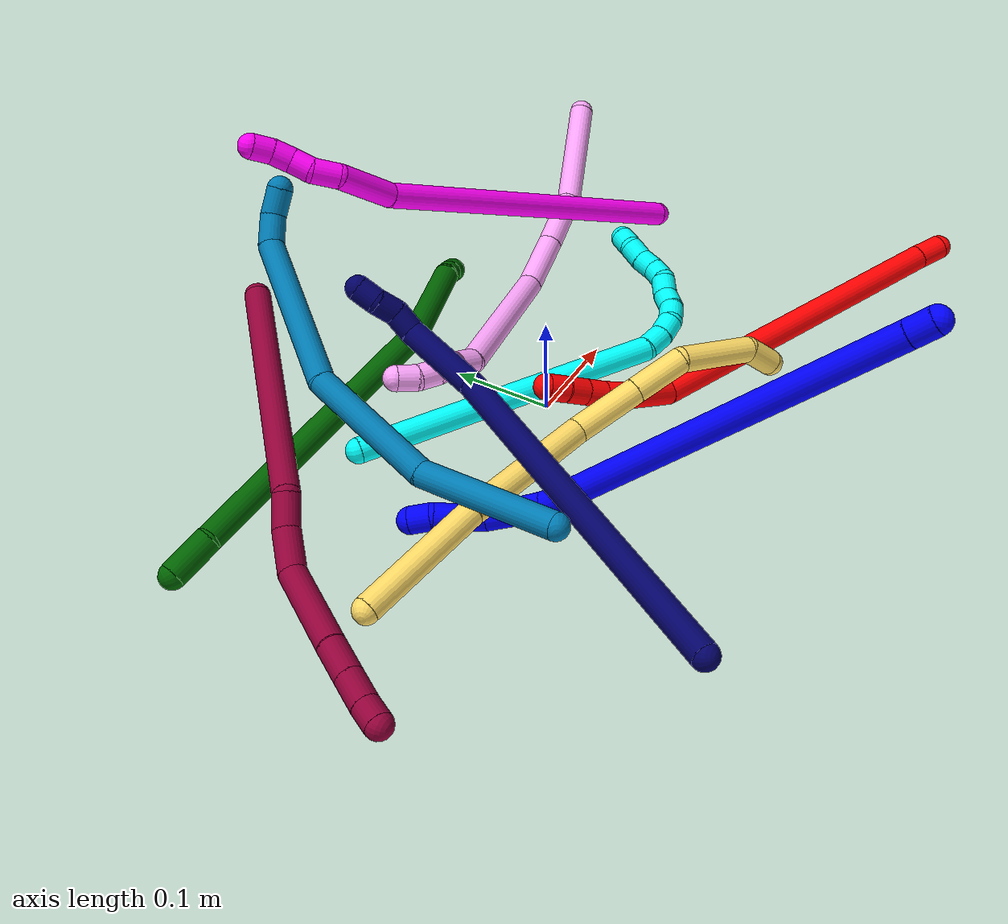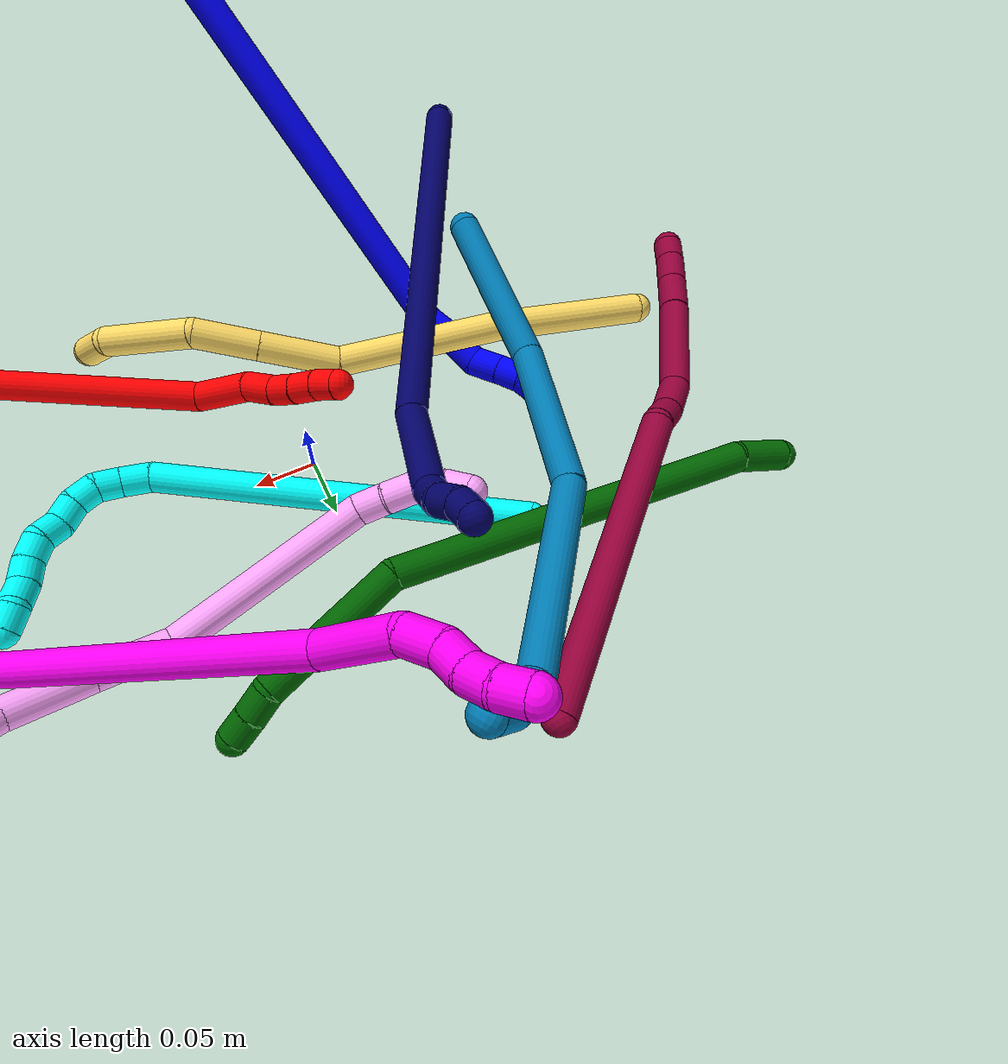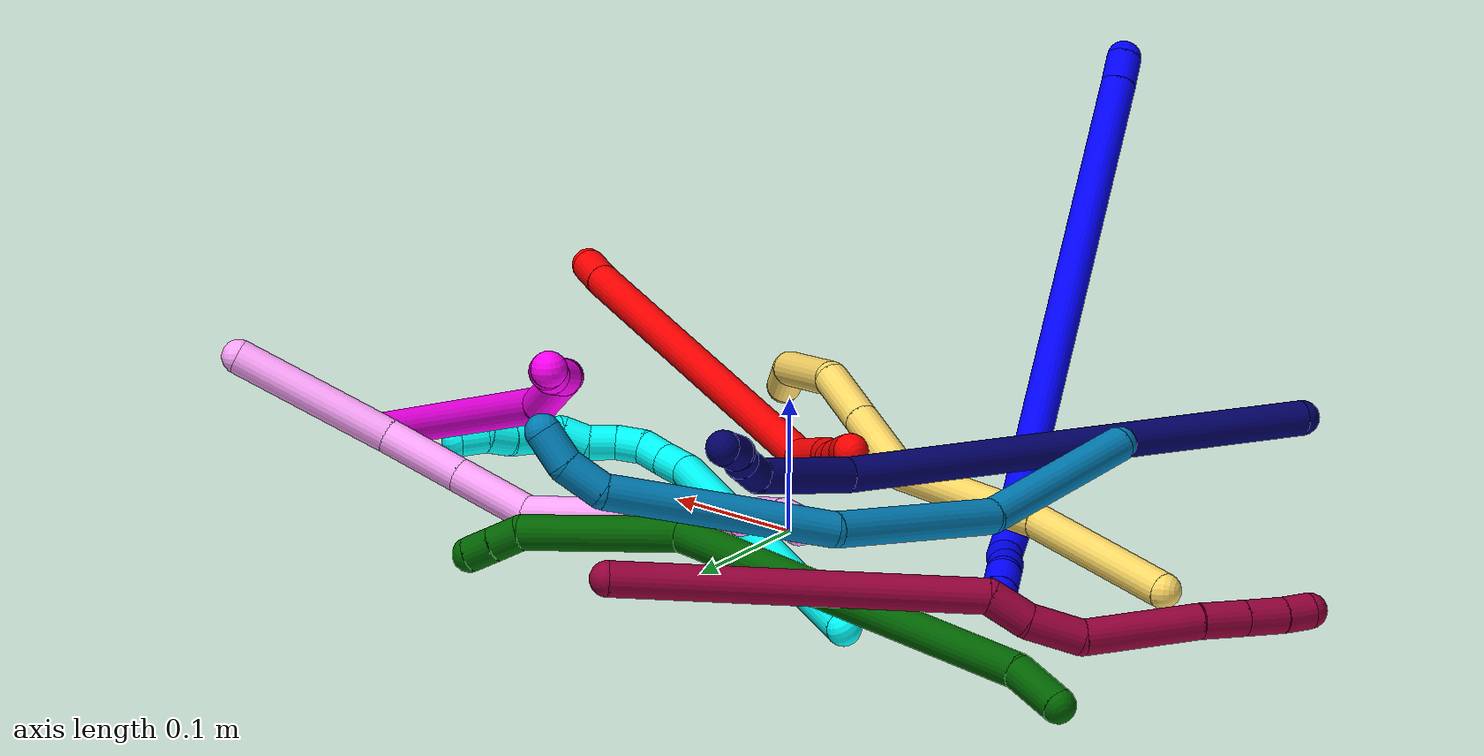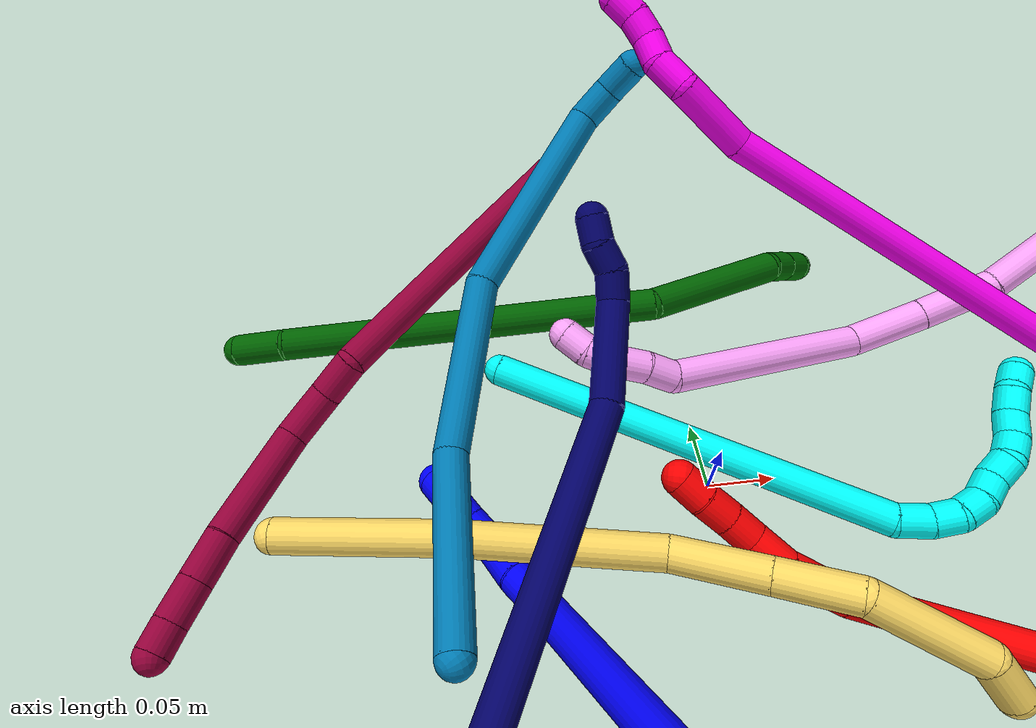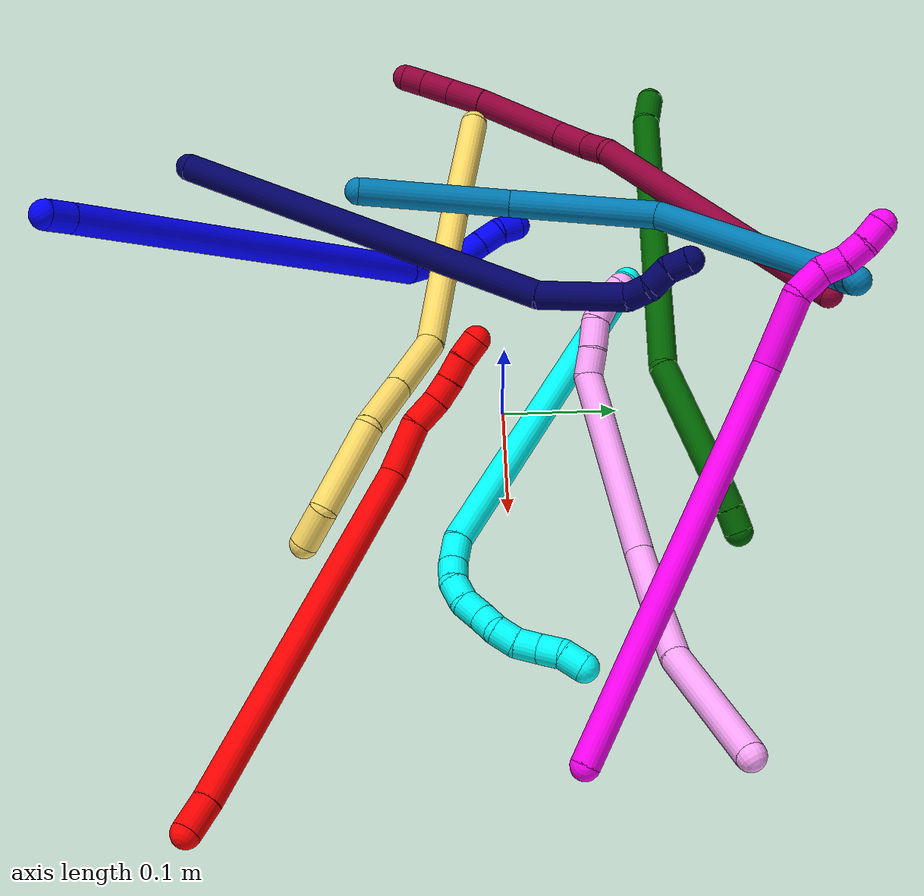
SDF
<sdf version="1.7">
 <world name="default">
  <plugin name="TubeGeneratorPlugin" filename="libtube_generator_plugin.so"/>
  <model name="photoneo_s_sensor">
   <static>1</static>
   <pose>0 0 2 1.57079 1.57079 3.14159</pose>
   <link name="link">
    <inertial><mass>0.1</mass></inertial>
    <sensor name="sensor" type="depth">
     <update_rate>30</update_rate>
     <camera>
      <horizontal_fov>1.22</horizontal_fov>
      <image><width>1920</width><height>1200</height><format>B8G8R8</format></image>
      <clip><near>0.1</near><far>2</far></clip>
      <depth_camera><output>points</output></depth_camera>
     </camera>
     <plugin name="camera_plugin" filename="libgazebo_ros_depth_camera.so">
      <baseline>0.2</baseline>
      <alwaysOn>1</alwaysOn>
      <updateRate>0.0</updateRate>
      <cameraName>camera_ir</cameraName>
      <imageTopicName>/camera/color/image_raw</imageTopicName>
      <cameraInfoTopicName>/camera/color/camera_info</cameraInfoTopicName>
      <depthImageTopicName>/camera/depth/image_raw</depthImageTopicName>
      <depthImageCameraInfoTopicName>/camera/depth/camera_info</depthImageCameraInfoTopicName>
      <pointCloudTopicName>/camera/depth/points</pointCloudTopicName>
      <frameName>fr_optical</frameName>
      <pointCloudCutoff>0.1</pointCloudCutoff>
      <pointCloudCutoffMax>2.0</pointCloudCutoffMax>
      <distortionK1>0</distortionK1>
      <distortionK2>0</distortionK2>
      <distortionK3>0</distortionK3>
      <distortionT1>0</distortionT1>
      <distortionT2>0</distortionT2>
      <CxPrime>0</CxPrime>
      <Cx>0</Cx>
      <Cy>0</Cy>
      <focalLength>0</focalLength>
      <hackBaseline>0</hackBaseline>
     </plugin>
    </sensor>
   </link>
  </model>
  <gravity>0 0 -9.8</gravity>
  <magnetic_field>6e-06 2.3e-05 -4.2e-05</magnetic_field>
  <atmosphere type="adiabatic"/>
  <physics name="default_physics" default="0" type="ode">
   <max_step_size>0.003</max_step_size>
   <real_time_factor>1</real_time_factor>
   <real_time_update_rate>1000</real_time_update_rate>
   <max_contacts>10000</max_contacts>
   <ode>
    <solver>
     <type>quick</type>
     <iters>100</iters>
     <sor>1.3</sor>
     <use_dynamic_moi_rescaling>0</use_dynamic_moi_rescaling>
    </solver>
    <constraints>
     <contact_max_correcting_vel>0</contact_max_correcting_vel>
     <contact_surface_layer>0.001</contact_surface_layer>
     <cfm>0</cfm>
     <erp>0.2</erp>
    </constraints>
   </ode>
  </physics>
  <scene><ambient>0.4 0.4 0.4 1</ambient><background>0.7 0.7 0.7 1</background><shadows>0</shadows></scene>
  <audio><device>default</device></audio>
  <spherical_coordinates>
   <surface_model>EARTH_WGS84</surface_model>
   <latitude_deg>0</latitude_deg>
   <longitude_deg>0</longitude_deg>
   <elevation>0</elevation>
   <heading_deg>0</heading_deg>
  </spherical_coordinates>
  <model name="bin">
   <static>1</static>
   <link name="bottom">
    <collision name="collision-bottom">
     <pose>0 0 -0.01 0 -0 0</pose>
     <geometry><box><size>0.8 0.6 0.02</size></box></geometry>
     <surface>
      <friction><ode><mu>100</mu><mu2>100</mu2></ode></friction>
      <contact><collide_bitmask>65535</collide_bitmask></contact>
     </surface>
    </collision>
   </link>
   <link name="west_wall">
    <collision name="collision-west_wall">
     <pose>-0.41 0 0.1 0 -0 0</pose>
     <geometry><box><size>0.02 0.6 0.2</size></box></geometry>
     <surface>
      <friction><ode><mu>100</mu><mu2>100</mu2></ode></friction>
      <contact><collide_bitmask>65535</collide_bitmask></contact>
     </surface>
    </collision>
   </link>
   <link name="east_wall">
    <collision name="collision-east_wall">
     <pose>0.41 0 0.1 0 -0 0</pose>
     <geometry><box><size>0.02 0.6 0.2</size></box></geometry>
     <surface>
      <friction><ode><mu>100</mu><mu2>100</mu2></ode></friction>
      <contact><collide_bitmask>65535</collide_bitmask></contact>
     </surface>
    </collision>
   </link>
   <link name="south_wall">
    <collision name="collision-south_wall">
     <pose>0 -0.31 0.1 0 -0 0</pose>
     <geometry><box><size>0.8 0.02 0.2</size></box></geometry>
     <surface>
      <friction><ode><mu>100</mu><mu2>100</mu2></ode></friction>
      <contact><collide_bitmask>65535</collide_bitmask></contact>
     </surface>
    </collision>
   </link>
   <link name="north_wall">
    <collision name="collision-north_wall">
     <pose>0 0.31 0.1 0 -0 0</pose>
     <geometry><box><size>0.8 0.02 0.2</size></box></geometry>
     <surface>
      <friction><ode><mu>100</mu><mu2>100</mu2></ode></friction>
      <contact><collide_bitmask>65535</collide_bitmask></contact>
     </surface>
    </collision>
   </link>
  </model>
  <model name="1">
   <static>0</static>
   <link name="1">
    <collision name="collision-cylinder-e_1_1_4">
     <pose>-0.002651 0.008505 -0.007513 -2.29433 -0.229488 0.50045</pose>
     <geometry><cylinder><radius>0.0125</radius><length>0.023308</length></cylinder></geometry>
     <surface>
      <friction><ode><mu>1.16</mu><mu2>1.16</mu2><slip1>0</slip1><slip2>0</slip2></ode></friction>
      <contact><ode><kp>1e+06</kp><kd>1</kd><max_vel>0</max_vel><min_depth>0.001</min_depth></ode></contact>
     </surface>
    </collision>
    <visual name="visual-cylinder-e_1_1_4">
     <pose>-0.002651 0.008505 -0.007513 -2.29433 -0.229488 0.50045</pose>
     <geometry><cylinder><radius>0.0125</radius><length>0.023308</length></cylinder></geometry>
     <material><ambient>0 0 1 1</ambient></material>
    </visual>
    <collision name="collision-cylinder-e_2_4_5">
     <pose>-0.049626 0.146205 -0.128973 -2.29357 -0.25184 0.546837</pose>
     <geometry><cylinder><radius>0.0125</radius><length>0.355751</length></cylinder></geometry>
     <surface>
      <friction><ode><mu>1.16</mu><mu2>1.16</mu2><slip1>0</slip1><slip2>0</slip2></ode></friction>
      <contact><ode><kp>1e+06</kp><kd>1</kd><max_vel>0</max_vel><min_depth>0.001</min_depth></ode></contact>
     </surface>
    </collision>
    <visual name="visual-cylinder-e_2_4_5">
     <pose>-0.049626 0.146205 -0.128973 -2.29357 -0.25184 0.546837</pose>
     <geometry><cylinder><radius>0.0125</radius><length>0.355751</length></cylinder></geometry>
     <material><ambient>0 0 1 1</ambient></material>
    </visual>
    <collision name="collision-cylinder-e_3_5_6">
     <pose>-0.094551 0.28094 -0.253103 -2.64327 -0.051768 0.202799</pose>
     <geometry><cylinder><radius>0.0125</radius><length>0.023217</length></cylinder></geometry>
     <surface>
      <friction><ode><mu>1.16</mu><mu2>1.16</mu2><slip1>0</slip1><slip2>0</slip2></ode></friction>
      <contact><ode><kp>1e+06</kp><kd>1</kd><max_vel>0</max_vel><min_depth>0.001</min_depth></ode></contact>
     </surface>
    </collision>
    <visual name="visual-cylinder-e_3_5_6">
     <pose>-0.094551 0.28094 -0.253103 -2.64327 -0.051768 0.202799</pose>
     <geometry><cylinder><radius>0.0125</radius><length>0.023217</length></cylinder></geometry>
     <material><ambient>0 0 1 1</ambient></material>
    </visual>
    <collision name="collision-cylinder-e_4_6_7">
     <pose>-0.097952 0.294004 -0.276473 -2.6231 -0.182414 0.664169</pose>
     <geometry><cylinder><radius>0.0125</radius><length>0.030877</length></cylinder></geometry>
     <surface>
      <friction><ode><mu>1.16</mu><mu2>1.16</mu2><slip1>0</slip1><slip2>0</slip2></ode></friction>
      <contact><ode><kp>1e+06</kp><kd>1</kd><max_vel>0</max_vel><min_depth>0.001</min_depth></ode></contact>
     </surface>
    </collision>
    <visual name="visual-cylinder-e_4_6_7">
     <pose>-0.097952 0.294004 -0.276473 -2.6231 -0.182414 0.664169</pose>
     <geometry><cylinder><radius>0.0125</radius><length>0.030877</length></cylinder></geometry>
     <material><ambient>0 0 1 1</ambient></material>
    </visual>
    <collision name="collision-cylinder-e_5_7_8">
     <pose>-0.098754 0.303241 -0.302122 -3.00506 0.157575 -1.71412</pose>
     <geometry><cylinder><radius>0.0125</radius><length>0.025474</length></cylinder></geometry>
     <surface>
      <friction><ode><mu>1.16</mu><mu2>1.16</mu2><slip1>0</slip1><slip2>0</slip2></ode></friction>
      <contact><ode><kp>1e+06</kp><kd>1</kd><max_vel>0</max_vel><min_depth>0.001</min_depth></ode></contact>
     </surface>
    </collision>
    <visual name="visual-cylinder-e_5_7_8">
     <pose>-0.098754 0.303241 -0.302122 -3.00506 0.157575 -1.71412</pose>
     <geometry><cylinder><radius>0.0125</radius><length>0.025474</length></cylinder></geometry>
     <material><ambient>0 0 1 1</ambient></material>
    </visual>
    <collision name="collision-cylinder-e_6_8_9">
     <pose>-0.095887 0.305842 -0.325121 -3.05736 0.081916 -1.54284</pose>
     <geometry><cylinder><radius>0.0125</radius><length>0.02122</length></cylinder></geometry>
     <surface>
      <friction><ode><mu>1.16</mu><mu2>1.16</mu2><slip1>0</slip1><slip2>0</slip2></ode></friction>
      <contact><ode><kp>1e+06</kp><kd>1</kd><max_vel>0</max_vel><min_depth>0.001</min_depth></ode></contact>
     </surface>
    </collision>
    <visual name="visual-cylinder-e_6_8_9">
     <pose>-0.095887 0.305842 -0.325121 -3.05736 0.081916 -1.54284</pose>
     <geometry><cylinder><radius>0.0125</radius><length>0.02122</length></cylinder></geometry>
     <material><ambient>0 0 1 1</ambient></material>
    </visual>
    <collision name="collision-cylinder-e_7_9_2">
     <pose>-0.095791 0.311067 -0.344722 -2.69549 -0.07672 0.33522</pose>
     <geometry><cylinder><radius>0.0125</radius><length>0.020153</length></cylinder></geometry>
     <surface>
      <friction><ode><mu>1.16</mu><mu2>1.16</mu2><slip1>0</slip1><slip2>0</slip2></ode></friction>
      <contact><ode><kp>1e+06</kp><kd>1</kd><max_vel>0</max_vel><min_depth>0.001</min_depth></ode></contact>
     </surface>
    </collision>
    <visual name="visual-cylinder-e_7_9_2">
     <pose>-0.095791 0.311067 -0.344722 -2.69549 -0.07672 0.33522</pose>
     <geometry><cylinder><radius>0.0125</radius><length>0.020153</length></cylinder></geometry>
     <material><ambient>0 0 1 1</ambient></material>
    </visual>
    <collision name="collision-sphere-2">
     <pose>-0.096564 0.315402 -0.353786 0 -0 0</pose>
     <geometry><sphere><radius>0.0125</radius></sphere></geometry>
     <surface>
      <friction><ode><mu>1.16</mu><mu2>1.16</mu2><slip1>0</slip1><slip2>0</slip2></ode></friction>
      <contact><ode><kp>1e+06</kp><kd>1</kd><max_vel>0</max_vel><min_depth>0.001</min_depth></ode></contact>
     </surface>
    </collision>
    <visual name="visual-sphere-2">
     <pose>-0.096564 0.315402 -0.353786 0 -0 0</pose>
     <geometry><sphere><radius>0.0125</radius></sphere></geometry>
     <material><ambient>0 0 1 1</ambient></material>
    </visual>
    <collision name="collision-sphere-9">
     <pose>-0.095019 0.306732 -0.335658 0 -0 0</pose>
     <geometry><sphere><radius>0.0125</radius></sphere></geometry>
     <surface>
      <friction><ode><mu>1.16</mu><mu2>1.16</mu2><slip1>0</slip1><slip2>0</slip2></ode></friction>
      <contact><ode><kp>1e+06</kp><kd>1</kd><max_vel>0</max_vel><min_depth>0.001</min_depth></ode></contact>
     </surface>
    </collision>
    <visual name="visual-sphere-9">
     <pose>-0.095019 0.306732 -0.335658 0 -0 0</pose>
     <geometry><sphere><radius>0.0125</radius></sphere></geometry>
     <material><ambient>0 0 1 1</ambient></material>
    </visual>
    <collision name="collision-sphere-4">
     <pose>-0.005302 0.01701 -0.015026 0 -0 0</pose>
     <geometry><sphere><radius>0.0125</radius></sphere></geometry>
     <surface>
      <friction><ode><mu>1.16</mu><mu2>1.16</mu2><slip1>0</slip1><slip2>0</slip2></ode></friction>
      <contact><ode><kp>1e+06</kp><kd>1</kd><max_vel>0</max_vel><min_depth>0.001</min_depth></ode></contact>
     </surface>
    </collision>
    <visual name="visual-sphere-4">
     <pose>-0.005302 0.01701 -0.015026 0 -0 0</pose>
     <geometry><sphere><radius>0.0125</radius></sphere></geometry>
     <material><ambient>0 0 1 1</ambient></material>
    </visual>
    <collision name="collision-sphere-1">
     <geometry><sphere><radius>0.0125</radius></sphere></geometry>
     <surface>
      <friction><ode><mu>1.16</mu><mu2>1.16</mu2><slip1>0</slip1><slip2>0</slip2></ode></friction>
      <contact><ode><kp>1e+06</kp><kd>1</kd><max_vel>0</max_vel><min_depth>0.001</min_depth></ode></contact>
     </surface>
    </collision>
    <visual name="visual-sphere-1">
     <geometry><sphere><radius>0.0125</radius></sphere></geometry>
     <material><ambient>0 0 1 1</ambient></material>
    </visual>
    <collision name="collision-sphere-8">
     <pose>-0.096755 0.304953 -0.314584 0 -0 0</pose>
     <geometry><sphere><radius>0.0125</radius></sphere></geometry>
     <surface>
      <friction><ode><mu>1.16</mu><mu2>1.16</mu2><slip1>0</slip1><slip2>0</slip2></ode></friction>
      <contact><ode><kp>1e+06</kp><kd>1</kd><max_vel>0</max_vel><min_depth>0.001</min_depth></ode></contact>
     </surface>
    </collision>
    <visual name="visual-sphere-8">
     <pose>-0.096755 0.304953 -0.314584 0 -0 0</pose>
     <geometry><sphere><radius>0.0125</radius></sphere></geometry>
     <material><ambient>0 0 1 1</ambient></material>
    </visual>
    <collision name="collision-sphere-5">
     <pose>-0.09395 0.275399 -0.24292 0 -0 0</pose>
     <geometry><sphere><radius>0.0125</radius></sphere></geometry>
     <surface>
      <friction><ode><mu>1.16</mu><mu2>1.16</mu2><slip1>0</slip1><slip2>0</slip2></ode></friction>
      <contact><ode><kp>1e+06</kp><kd>1</kd><max_vel>0</max_vel><min_depth>0.001</min_depth></ode></contact>
     </surface>
    </collision>
    <visual name="visual-sphere-5">
     <pose>-0.09395 0.275399 -0.24292 0 -0 0</pose>
     <geometry><sphere><radius>0.0125</radius></sphere></geometry>
     <material><ambient>0 0 1 1</ambient></material>
    </visual>
    <collision name="collision-sphere-6">
     <pose>-0.095152 0.28648 -0.263286 0 -0 0</pose>
     <geometry><sphere><radius>0.0125</radius></sphere></geometry>
     <surface>
      <friction><ode><mu>1.16</mu><mu2>1.16</mu2><slip1>0</slip1><slip2>0</slip2></ode></friction>
      <contact><ode><kp>1e+06</kp><kd>1</kd><max_vel>0</max_vel><min_depth>0.001</min_depth></ode></contact>
     </surface>
    </collision>
    <visual name="visual-sphere-6">
     <pose>-0.095152 0.28648 -0.263286 0 -0 0</pose>
     <geometry><sphere><radius>0.0125</radius></sphere></geometry>
     <material><ambient>0 0 1 1</ambient></material>
    </visual>
    <collision name="collision-sphere-7">
     <pose>-0.100753 0.301528 -0.28966 0 -0 0</pose>
     <geometry><sphere><radius>0.0125</radius></sphere></geometry>
     <surface>
      <friction><ode><mu>1.16</mu><mu2>1.16</mu2><slip1>0</slip1><slip2>0</slip2></ode></friction>
      <contact><ode><kp>1e+06</kp><kd>1</kd><max_vel>0</max_vel><min_depth>0.001</min_depth></ode></contact>
     </surface>
    </collision>
    <visual name="visual-sphere-7">
     <pose>-0.100753 0.301528 -0.28966 0 -0 0</pose>
     <geometry><sphere><radius>0.0125</radius></sphere></geometry>
     <material><ambient>0 0 1 1</ambient></material>
    </visual>
    <inertial>
     <pose>-0.058834 0.17659 -0.164026 0 -0 0</pose>
     <mass>0.5</mass>
     <inertia>
      <ixx>0.005012</ixx>
      <ixy>0</ixy>
      <ixz>0</ixz>
      <iyy>0.000154</iyy>
      <iyz>0</iyz>
      <izz>-0.001829</izz>
     </inertia>
    </inertial>
   </link>
   <pose>-0.029151 -0.355736 0.262166 -1.78232 -0.227384 -2.61819</pose>
  </model>
  <model name="2">
   <static>0</static>
   <link name="2">
    <collision name="collision-cylinder-e_1_1_4">
     <pose>-0.000634 0.002515 -0.01429 -2.96739 -0.043676 0.490206</pose>
     <geometry><cylinder><radius>0.0125</radius><length>0.029047</length></cylinder></geometry>
     <surface>
      <friction><ode><mu>1.16</mu><mu2>1.16</mu2><slip1>0</slip1><slip2>0</slip2></ode></friction>
      <contact><ode><kp>1e+06</kp><kd>1</kd><max_vel>0</max_vel><min_depth>0.001</min_depth></ode></contact>
     </surface>
    </collision>
    <visual name="visual-cylinder-e_1_1_4">
     <pose>-0.000634 0.002515 -0.01429 -2.96739 -0.043676 0.490206</pose>
     <geometry><cylinder><radius>0.0125</radius><length>0.029047</length></cylinder></geometry>
     <material><ambient>1 0 0 1</ambient></material>
    </visual>
    <collision name="collision-cylinder-e_2_4_5">
     <pose>-0.01344 0.024268 -0.193041 -3.02514 -0.073379 1.12395</pose>
     <geometry><cylinder><radius>0.0125</radius><length>0.332058</length></cylinder></geometry>
     <surface>
      <friction><ode><mu>1.16</mu><mu2>1.16</mu2><slip1>0</slip1><slip2>0</slip2></ode></friction>
      <contact><ode><kp>1e+06</kp><kd>1</kd><max_vel>0</max_vel><min_depth>0.001</min_depth></ode></contact>
     </surface>
    </collision>
    <visual name="visual-cylinder-e_2_4_5">
     <pose>-0.01344 0.024268 -0.193041 -3.02514 -0.073379 1.12395</pose>
     <geometry><cylinder><radius>0.0125</radius><length>0.332058</length></cylinder></geometry>
     <material><ambient>1 0 0 1</ambient></material>
    </visual>
    <collision name="collision-cylinder-e_3_5_6">
     <pose>-0.037062 0.047828 -0.378254 -2.93627 -0.495257 2.36768</pose>
     <geometry><cylinder><radius>0.0125</radius><length>0.048183</length></cylinder></geometry>
     <surface>
      <friction><ode><mu>1.16</mu><mu2>1.16</mu2><slip1>0</slip1><slip2>0</slip2></ode></friction>
      <contact><ode><kp>1e+06</kp><kd>1</kd><max_vel>0</max_vel><min_depth>0.001</min_depth></ode></contact>
     </surface>
    </collision>
    <visual name="visual-cylinder-e_3_5_6">
     <pose>-0.037062 0.047828 -0.378254 -2.93627 -0.495257 2.36768</pose>
     <geometry><cylinder><radius>0.0125</radius><length>0.048183</length></cylinder></geometry>
     <material><ambient>1 0 0 1</ambient></material>
    </visual>
    <collision name="collision-cylinder-e_4_6_7">
     <pose>-0.053186 0.058539 -0.410116 -2.61971 -0.349667 1.16881</pose>
     <geometry><cylinder><radius>0.0125</radius><length>0.027284</length></cylinder></geometry>
     <surface>
      <friction><ode><mu>1.16</mu><mu2>1.16</mu2><slip1>0</slip1><slip2>0</slip2></ode></friction>
      <contact><ode><kp>1e+06</kp><kd>1</kd><max_vel>0</max_vel><min_depth>0.001</min_depth></ode></contact>
     </surface>
    </collision>
    <visual name="visual-cylinder-e_4_6_7">
     <pose>-0.053186 0.058539 -0.410116 -2.61971 -0.349667 1.16881</pose>
     <geometry><cylinder><radius>0.0125</radius><length>0.027284</length></cylinder></geometry>
     <material><ambient>1 0 0 1</ambient></material>
    </visual>
    <collision name="collision-cylinder-e_5_7_8">
     <pose>-0.063353 0.068989 -0.429399 -2.68048 -0.541872 1.73835</pose>
     <geometry><cylinder><radius>0.0125</radius><length>0.021304</length></cylinder></geometry>
     <surface>
      <friction><ode><mu>1.16</mu><mu2>1.16</mu2><slip1>0</slip1><slip2>0</slip2></ode></friction>
      <contact><ode><kp>1e+06</kp><kd>1</kd><max_vel>0</max_vel><min_depth>0.001</min_depth></ode></contact>
     </surface>
    </collision>
    <visual name="visual-cylinder-e_5_7_8">
     <pose>-0.063353 0.068989 -0.429399 -2.68048 -0.541872 1.73835</pose>
     <geometry><cylinder><radius>0.0125</radius><length>0.021304</length></cylinder></geometry>
     <material><ambient>1 0 0 1</ambient></material>
    </visual>
    <collision name="collision-cylinder-e_6_8_9">
     <pose>-0.074879 0.076478 -0.445913 -2.75159 -0.589507 1.98803</pose>
     <geometry><cylinder><radius>0.0125</radius><length>0.021699</length></cylinder></geometry>
     <surface>
      <friction><ode><mu>1.16</mu><mu2>1.16</mu2><slip1>0</slip1><slip2>0</slip2></ode></friction>
      <contact><ode><kp>1e+06</kp><kd>1</kd><max_vel>0</max_vel><min_depth>0.001</min_depth></ode></contact>
     </surface>
    </collision>
    <visual name="visual-cylinder-e_6_8_9">
     <pose>-0.074879 0.076478 -0.445913 -2.75159 -0.589507 1.98803</pose>
     <geometry><cylinder><radius>0.0125</radius><length>0.021699</length></cylinder></geometry>
     <material><ambient>1 0 0 1</ambient></material>
    </visual>
    <collision name="collision-cylinder-e_7_9_2">
     <pose>-0.085815 0.084194 -0.462119 -2.64251 -0.500946 1.57469</pose>
     <geometry><cylinder><radius>0.0125</radius><length>0.020424</length></cylinder></geometry>
     <surface>
      <friction><ode><mu>1.16</mu><mu2>1.16</mu2><slip1>0</slip1><slip2>0</slip2></ode></friction>
      <contact><ode><kp>1e+06</kp><kd>1</kd><max_vel>0</max_vel><min_depth>0.001</min_depth></ode></contact>
     </surface>
    </collision>
    <visual name="visual-cylinder-e_7_9_2">
     <pose>-0.085815 0.084194 -0.462119 -2.64251 -0.500946 1.57469</pose>
     <geometry><cylinder><radius>0.0125</radius><length>0.020424</length></cylinder></geometry>
     <material><ambient>1 0 0 1</ambient></material>
    </visual>
    <collision name="collision-sphere-2">
     <pose>-0.090719 0.088481 -0.469984 0 -0 0</pose>
     <geometry><sphere><radius>0.0125</radius></sphere></geometry>
     <surface>
      <friction><ode><mu>1.16</mu><mu2>1.16</mu2><slip1>0</slip1><slip2>0</slip2></ode></friction>
      <contact><ode><kp>1e+06</kp><kd>1</kd><max_vel>0</max_vel><min_depth>0.001</min_depth></ode></contact>
     </surface>
    </collision>
    <visual name="visual-sphere-2">
     <pose>-0.090719 0.088481 -0.469984 0 -0 0</pose>
     <geometry><sphere><radius>0.0125</radius></sphere></geometry>
     <material><ambient>1 0 0 1</ambient></material>
    </visual>
    <collision name="collision-sphere-9">
     <pose>-0.08091 0.079907 -0.454254 0 -0 0</pose>
     <geometry><sphere><radius>0.0125</radius></sphere></geometry>
     <surface>
      <friction><ode><mu>1.16</mu><mu2>1.16</mu2><slip1>0</slip1><slip2>0</slip2></ode></friction>
      <contact><ode><kp>1e+06</kp><kd>1</kd><max_vel>0</max_vel><min_depth>0.001</min_depth></ode></contact>
     </surface>
    </collision>
    <visual name="visual-sphere-9">
     <pose>-0.08091 0.079907 -0.454254 0 -0 0</pose>
     <geometry><sphere><radius>0.0125</radius></sphere></geometry>
     <material><ambient>1 0 0 1</ambient></material>
    </visual>
    <collision name="collision-sphere-4">
     <pose>-0.001268 0.00503 -0.02858 0 -0 0</pose>
     <geometry><sphere><radius>0.0125</radius></sphere></geometry>
     <surface>
      <friction><ode><mu>1.16</mu><mu2>1.16</mu2><slip1>0</slip1><slip2>0</slip2></ode></friction>
      <contact><ode><kp>1e+06</kp><kd>1</kd><max_vel>0</max_vel><min_depth>0.001</min_depth></ode></contact>
     </surface>
    </collision>
    <visual name="visual-sphere-4">
     <pose>-0.001268 0.00503 -0.02858 0 -0 0</pose>
     <geometry><sphere><radius>0.0125</radius></sphere></geometry>
     <material><ambient>1 0 0 1</ambient></material>
    </visual>
    <collision name="collision-sphere-1">
     <geometry><sphere><radius>0.0125</radius></sphere></geometry>
     <surface>
      <friction><ode><mu>1.16</mu><mu2>1.16</mu2><slip1>0</slip1><slip2>0</slip2></ode></friction>
      <contact><ode><kp>1e+06</kp><kd>1</kd><max_vel>0</max_vel><min_depth>0.001</min_depth></ode></contact>
     </surface>
    </collision>
    <visual name="visual-sphere-1">
     <geometry><sphere><radius>0.0125</radius></sphere></geometry>
     <material><ambient>1 0 0 1</ambient></material>
    </visual>
    <collision name="collision-sphere-8">
     <pose>-0.068847 0.07305 -0.437572 0 -0 0</pose>
     <geometry><sphere><radius>0.0125</radius></sphere></geometry>
     <surface>
      <friction><ode><mu>1.16</mu><mu2>1.16</mu2><slip1>0</slip1><slip2>0</slip2></ode></friction>
      <contact><ode><kp>1e+06</kp><kd>1</kd><max_vel>0</max_vel><min_depth>0.001</min_depth></ode></contact>
     </surface>
    </collision>
    <visual name="visual-sphere-8">
     <pose>-0.068847 0.07305 -0.437572 0 -0 0</pose>
     <geometry><sphere><radius>0.0125</radius></sphere></geometry>
     <material><ambient>1 0 0 1</ambient></material>
    </visual>
    <collision name="collision-sphere-5">
     <pose>-0.025613 0.043507 -0.357502 0 -0 0</pose>
     <geometry><sphere><radius>0.0125</radius></sphere></geometry>
     <surface>
      <friction><ode><mu>1.16</mu><mu2>1.16</mu2><slip1>0</slip1><slip2>0</slip2></ode></friction>
      <contact><ode><kp>1e+06</kp><kd>1</kd><max_vel>0</max_vel><min_depth>0.001</min_depth></ode></contact>
     </surface>
    </collision>
    <visual name="visual-sphere-5">
     <pose>-0.025613 0.043507 -0.357502 0 -0 0</pose>
     <geometry><sphere><radius>0.0125</radius></sphere></geometry>
     <material><ambient>1 0 0 1</ambient></material>
    </visual>
    <collision name="collision-sphere-6">
     <pose>-0.048512 0.05215 -0.399005 0 -0 0</pose>
     <geometry><sphere><radius>0.0125</radius></sphere></geometry>
     <surface>
      <friction><ode><mu>1.16</mu><mu2>1.16</mu2><slip1>0</slip1><slip2>0</slip2></ode></friction>
      <contact><ode><kp>1e+06</kp><kd>1</kd><max_vel>0</max_vel><min_depth>0.001</min_depth></ode></contact>
     </surface>
    </collision>
    <visual name="visual-sphere-6">
     <pose>-0.048512 0.05215 -0.399005 0 -0 0</pose>
     <geometry><sphere><radius>0.0125</radius></sphere></geometry>
     <material><ambient>1 0 0 1</ambient></material>
    </visual>
    <collision name="collision-sphere-7">
     <pose>-0.057859 0.064928 -0.421226 0 -0 0</pose>
     <geometry><sphere><radius>0.0125</radius></sphere></geometry>
     <surface>
      <friction><ode><mu>1.16</mu><mu2>1.16</mu2><slip1>0</slip1><slip2>0</slip2></ode></friction>
      <contact><ode><kp>1e+06</kp><kd>1</kd><max_vel>0</max_vel><min_depth>0.001</min_depth></ode></contact>
     </surface>
    </collision>
    <visual name="visual-sphere-7">
     <pose>-0.057859 0.064928 -0.421226 0 -0 0</pose>
     <geometry><sphere><radius>0.0125</radius></sphere></geometry>
     <material><ambient>1 0 0 1</ambient></material>
    </visual>
    <inertial>
     <pose>-0.024891 0.033764 -0.244387 0 -0 0</pose>
     <mass>0.5</mass>
     <inertia>
      <ixx>0.00408</ixx>
      <ixy>0</ixy>
      <ixz>0</ixz>
      <iyy>0.001493</iyy>
      <iyz>0</iyz>
      <izz>-0.000164</izz>
     </inertia>
    </inertial>
   </link>
   <pose>0.388501 -0.256791 0.038923 0.697591 1.35597 0.359934</pose>
  </model>
  <model name="3">
   <static>0</static>
   <link name="3">
    <collision name="collision-cylinder-e_1_1_4">
     <pose>0.138157 -0.073204 -0.004298 1.62945 1.08284 1.13537</pose>
     <geometry><cylinder><radius>0.0125</radius><length>0.312823</length></cylinder></geometry>
     <surface>
      <friction><ode><mu>1.16</mu><mu2>1.16</mu2><slip1>0</slip1><slip2>0</slip2></ode></friction>
      <contact><ode><kp>1e+06</kp><kd>1</kd><max_vel>0</max_vel><min_depth>0.001</min_depth></ode></contact>
     </surface>
    </collision>
    <visual name="visual-cylinder-e_1_1_4">
     <pose>0.138157 -0.073204 -0.004298 1.62945 1.08284 1.13537</pose>
     <geometry><cylinder><radius>0.0125</radius><length>0.312823</length></cylinder></geometry>
     <material><ambient>0.003922 1 0.996078 1</ambient></material>
    </visual>
    <collision name="collision-cylinder-e_2_4_5">
     <pose>0.288252 -0.148727 -0.006095 0.747762 1.29242 0.57541</pose>
     <geometry><cylinder><radius>0.0125</radius><length>0.024833</length></cylinder></geometry>
     <surface>
      <friction><ode><mu>1.16</mu><mu2>1.16</mu2><slip1>0</slip1><slip2>0</slip2></ode></friction>
      <contact><ode><kp>1e+06</kp><kd>1</kd><max_vel>0</max_vel><min_depth>0.001</min_depth></ode></contact>
     </surface>
    </collision>
    <visual name="visual-cylinder-e_2_4_5">
     <pose>0.288252 -0.148727 -0.006095 0.747762 1.29242 0.57541</pose>
     <geometry><cylinder><radius>0.0125</radius><length>0.024833</length></cylinder></geometry>
     <material><ambient>0.003922 1 0.996078 1</ambient></material>
    </visual>
    <collision name="collision-cylinder-e_3_5_6">
     <pose>0.309434 -0.15204 0.000753 0.224431 1.12141 0.141286</pose>
     <geometry><cylinder><radius>0.0125</radius><length>0.020525</length></cylinder></geometry>
     <surface>
      <friction><ode><mu>1.16</mu><mu2>1.16</mu2><slip1>0</slip1><slip2>0</slip2></ode></friction>
      <contact><ode><kp>1e+06</kp><kd>1</kd><max_vel>0</max_vel><min_depth>0.001</min_depth></ode></contact>
     </surface>
    </collision>
    <visual name="visual-cylinder-e_3_5_6">
     <pose>0.309434 -0.15204 0.000753 0.224431 1.12141 0.141286</pose>
     <geometry><cylinder><radius>0.0125</radius><length>0.020525</length></cylinder></geometry>
     <material><ambient>0.003922 1 0.996078 1</ambient></material>
    </visual>
    <collision name="collision-cylinder-e_4_6_7">
     <pose>0.327327 -0.149508 0.009386 -0.687976 1.0004 -0.386699</pose>
     <geometry><cylinder><radius>0.0125</radius><length>0.020554</length></cylinder></geometry>
     <surface>
      <friction><ode><mu>1.16</mu><mu2>1.16</mu2><slip1>0</slip1><slip2>0</slip2></ode></friction>
      <contact><ode><kp>1e+06</kp><kd>1</kd><max_vel>0</max_vel><min_depth>0.001</min_depth></ode></contact>
     </surface>
    </collision>
    <visual name="visual-cylinder-e_4_6_7">
     <pose>0.327327 -0.149508 0.009386 -0.687976 1.0004 -0.386699</pose>
     <geometry><cylinder><radius>0.0125</radius><length>0.020554</length></cylinder></geometry>
     <material><ambient>0.003922 1 0.996078 1</ambient></material>
    </visual>
    <collision name="collision-cylinder-e_5_7_8">
     <pose>0.342434 -0.139325 0.018366 -0.956951 0.670161 -0.357365</pose>
     <geometry><cylinder><radius>0.0125</radius><length>0.020789</length></cylinder></geometry>
     <surface>
      <friction><ode><mu>1.16</mu><mu2>1.16</mu2><slip1>0</slip1><slip2>0</slip2></ode></friction>
      <contact><ode><kp>1e+06</kp><kd>1</kd><max_vel>0</max_vel><min_depth>0.001</min_depth></ode></contact>
     </surface>
    </collision>
    <visual name="visual-cylinder-e_5_7_8">
     <pose>0.342434 -0.139325 0.018366 -0.956951 0.670161 -0.357365</pose>
     <geometry><cylinder><radius>0.0125</radius><length>0.020789</length></cylinder></geometry>
     <material><ambient>0.003922 1 0.996078 1</ambient></material>
    </visual>
    <collision name="collision-cylinder-e_6_8_9">
     <pose>0.355185 -0.129163 0.030053 -0.464281 0.677576 -0.16622</pose>
     <geometry><cylinder><radius>0.0125</radius><length>0.020082</length></cylinder></geometry>
     <surface>
      <friction><ode><mu>1.16</mu><mu2>1.16</mu2><slip1>0</slip1><slip2>0</slip2></ode></friction>
      <contact><ode><kp>1e+06</kp><kd>1</kd><max_vel>0</max_vel><min_depth>0.001</min_depth></ode></contact>
     </surface>
    </collision>
    <visual name="visual-cylinder-e_6_8_9">
     <pose>0.355185 -0.129163 0.030053 -0.464281 0.677576 -0.16622</pose>
     <geometry><cylinder><radius>0.0125</radius><length>0.020082</length></cylinder></geometry>
     <material><ambient>0.003922 1 0.996078 1</ambient></material>
    </visual>
    <collision name="collision-cylinder-e_7_9_10">
     <pose>0.366541 -0.118111 0.041249 -1.06292 0.529953 -0.316386</pose>
     <geometry><cylinder><radius>0.0125</radius><length>0.020026</length></cylinder></geometry>
     <surface>
      <friction><ode><mu>1.16</mu><mu2>1.16</mu2><slip1>0</slip1><slip2>0</slip2></ode></friction>
      <contact><ode><kp>1e+06</kp><kd>1</kd><max_vel>0</max_vel><min_depth>0.001</min_depth></ode></contact>
     </surface>
    </collision>
    <visual name="visual-cylinder-e_7_9_10">
     <pose>0.366541 -0.118111 0.041249 -1.06292 0.529953 -0.316386</pose>
     <geometry><cylinder><radius>0.0125</radius><length>0.020026</length></cylinder></geometry>
     <material><ambient>0.003922 1 0.996078 1</ambient></material>
    </visual>
    <collision name="collision-cylinder-e_8_10_11">
     <pose>0.373842 -0.102319 0.050891 -0.987389 0.222951 -0.120334</pose>
     <geometry><cylinder><radius>0.0125</radius><length>0.020255</length></cylinder></geometry>
     <surface>
      <friction><ode><mu>1.16</mu><mu2>1.16</mu2><slip1>0</slip1><slip2>0</slip2></ode></friction>
      <contact><ode><kp>1e+06</kp><kd>1</kd><max_vel>0</max_vel><min_depth>0.001</min_depth></ode></contact>
     </surface>
    </collision>
    <visual name="visual-cylinder-e_8_10_11">
     <pose>0.373842 -0.102319 0.050891 -0.987389 0.222951 -0.120334</pose>
     <geometry><cylinder><radius>0.0125</radius><length>0.020255</length></cylinder></geometry>
     <material><ambient>0.003922 1 0.996078 1</ambient></material>
    </visual>
    <collision name="collision-cylinder-e_9_11_12">
     <pose>0.37854 -0.087275 0.063304 -0.773012 0.24736 -0.1011</pose>
     <geometry><cylinder><radius>0.0125</radius><length>0.020092</length></cylinder></geometry>
     <surface>
      <friction><ode><mu>1.16</mu><mu2>1.16</mu2><slip1>0</slip1><slip2>0</slip2></ode></friction>
      <contact><ode><kp>1e+06</kp><kd>1</kd><max_vel>0</max_vel><min_depth>0.001</min_depth></ode></contact>
     </surface>
    </collision>
    <visual name="visual-cylinder-e_9_11_12">
     <pose>0.37854 -0.087275 0.063304 -0.773012 0.24736 -0.1011</pose>
     <geometry><cylinder><radius>0.0125</radius><length>0.020092</length></cylinder></geometry>
     <material><ambient>0.003922 1 0.996078 1</ambient></material>
    </visual>
    <collision name="collision-cylinder-e_10_12_2">
     <pose>0.386054 -0.072851 0.074349 -1.08011 0.529131 -0.322021</pose>
     <geometry><cylinder><radius>0.0125</radius><length>0.020022</length></cylinder></geometry>
     <surface>
      <friction><ode><mu>1.16</mu><mu2>1.16</mu2><slip1>0</slip1><slip2>0</slip2></ode></friction>
      <contact><ode><kp>1e+06</kp><kd>1</kd><max_vel>0</max_vel><min_depth>0.001</min_depth></ode></contact>
     </surface>
    </collision>
    <visual name="visual-cylinder-e_10_12_2">
     <pose>0.386054 -0.072851 0.074349 -1.08011 0.529131 -0.322021</pose>
     <geometry><cylinder><radius>0.0125</radius><length>0.020022</length></cylinder></geometry>
     <material><ambient>0.003922 1 0.996078 1</ambient></material>
    </visual>
    <collision name="collision-sphere-2">
     <pose>0.391107 -0.065228 0.078421 0 -0 0</pose>
     <geometry><sphere><radius>0.0125</radius></sphere></geometry>
     <surface>
      <friction><ode><mu>1.16</mu><mu2>1.16</mu2><slip1>0</slip1><slip2>0</slip2></ode></friction>
      <contact><ode><kp>1e+06</kp><kd>1</kd><max_vel>0</max_vel><min_depth>0.001</min_depth></ode></contact>
     </surface>
    </collision>
    <visual name="visual-sphere-2">
     <pose>0.391107 -0.065228 0.078421 0 -0 0</pose>
     <geometry><sphere><radius>0.0125</radius></sphere></geometry>
     <material><ambient>0.003922 1 0.996078 1</ambient></material>
    </visual>
    <collision name="collision-sphere-12">
     <pose>0.381 -0.080473 0.070276 0 -0 0</pose>
     <geometry><sphere><radius>0.0125</radius></sphere></geometry>
     <surface>
      <friction><ode><mu>1.16</mu><mu2>1.16</mu2><slip1>0</slip1><slip2>0</slip2></ode></friction>
      <contact><ode><kp>1e+06</kp><kd>1</kd><max_vel>0</max_vel><min_depth>0.001</min_depth></ode></contact>
     </surface>
    </collision>
    <visual name="visual-sphere-12">
     <pose>0.381 -0.080473 0.070276 0 -0 0</pose>
     <geometry><sphere><radius>0.0125</radius></sphere></geometry>
     <material><ambient>0.003922 1 0.996078 1</ambient></material>
    </visual>
    <collision name="collision-sphere-11">
     <pose>0.376081 -0.094076 0.056332 0 -0 0</pose>
     <geometry><sphere><radius>0.0125</radius></sphere></geometry>
     <surface>
      <friction><ode><mu>1.16</mu><mu2>1.16</mu2><slip1>0</slip1><slip2>0</slip2></ode></friction>
      <contact><ode><kp>1e+06</kp><kd>1</kd><max_vel>0</max_vel><min_depth>0.001</min_depth></ode></contact>
     </surface>
    </collision>
    <visual name="visual-sphere-11">
     <pose>0.376081 -0.094076 0.056332 0 -0 0</pose>
     <geometry><sphere><radius>0.0125</radius></sphere></geometry>
     <material><ambient>0.003922 1 0.996078 1</ambient></material>
    </visual>
    <collision name="collision-sphere-10">
     <pose>0.371602 -0.110562 0.045451 0 -0 0</pose>
     <geometry><sphere><radius>0.0125</radius></sphere></geometry>
     <surface>
      <friction><ode><mu>1.16</mu><mu2>1.16</mu2><slip1>0</slip1><slip2>0</slip2></ode></friction>
      <contact><ode><kp>1e+06</kp><kd>1</kd><max_vel>0</max_vel><min_depth>0.001</min_depth></ode></contact>
     </surface>
    </collision>
    <visual name="visual-sphere-10">
     <pose>0.371602 -0.110562 0.045451 0 -0 0</pose>
     <geometry><sphere><radius>0.0125</radius></sphere></geometry>
     <material><ambient>0.003922 1 0.996078 1</ambient></material>
    </visual>
    <collision name="collision-sphere-9">
     <pose>0.361479 -0.12566 0.037047 0 -0 0</pose>
     <geometry><sphere><radius>0.0125</radius></sphere></geometry>
     <surface>
      <friction><ode><mu>1.16</mu><mu2>1.16</mu2><slip1>0</slip1><slip2>0</slip2></ode></friction>
      <contact><ode><kp>1e+06</kp><kd>1</kd><max_vel>0</max_vel><min_depth>0.001</min_depth></ode></contact>
     </surface>
    </collision>
    <visual name="visual-sphere-9">
     <pose>0.361479 -0.12566 0.037047 0 -0 0</pose>
     <geometry><sphere><radius>0.0125</radius></sphere></geometry>
     <material><ambient>0.003922 1 0.996078 1</ambient></material>
    </visual>
    <collision name="collision-sphere-4">
     <pose>0.276313 -0.146407 -0.008597 0 -0 0</pose>
     <geometry><sphere><radius>0.0125</radius></sphere></geometry>
     <surface>
      <friction><ode><mu>1.16</mu><mu2>1.16</mu2><slip1>0</slip1><slip2>0</slip2></ode></friction>
      <contact><ode><kp>1e+06</kp><kd>1</kd><max_vel>0</max_vel><min_depth>0.001</min_depth></ode></contact>
     </surface>
    </collision>
    <visual name="visual-sphere-4">
     <pose>0.276313 -0.146407 -0.008597 0 -0 0</pose>
     <geometry><sphere><radius>0.0125</radius></sphere></geometry>
     <material><ambient>0.003922 1 0.996078 1</ambient></material>
    </visual>
    <collision name="collision-sphere-1">
     <geometry><sphere><radius>0.0125</radius></sphere></geometry>
     <surface>
      <friction><ode><mu>1.16</mu><mu2>1.16</mu2><slip1>0</slip1><slip2>0</slip2></ode></friction>
      <contact><ode><kp>1e+06</kp><kd>1</kd><max_vel>0</max_vel><min_depth>0.001</min_depth></ode></contact>
     </surface>
    </collision>
    <visual name="visual-sphere-1">
     <geometry><sphere><radius>0.0125</radius></sphere></geometry>
     <material><ambient>0.003922 1 0.996078 1</ambient></material>
    </visual>
    <collision name="collision-sphere-8">
     <pose>0.34889 -0.132666 0.023058 0 -0 0</pose>
     <geometry><sphere><radius>0.0125</radius></sphere></geometry>
     <surface>
      <friction><ode><mu>1.16</mu><mu2>1.16</mu2><slip1>0</slip1><slip2>0</slip2></ode></friction>
      <contact><ode><kp>1e+06</kp><kd>1</kd><max_vel>0</max_vel><min_depth>0.001</min_depth></ode></contact>
     </surface>
    </collision>
    <visual name="visual-sphere-8">
     <pose>0.34889 -0.132666 0.023058 0 -0 0</pose>
     <geometry><sphere><radius>0.0125</radius></sphere></geometry>
     <material><ambient>0.003922 1 0.996078 1</ambient></material>
    </visual>
    <collision name="collision-sphere-5">
     <pose>0.30019 -0.151047 -0.003594 0 -0 0</pose>
     <geometry><sphere><radius>0.0125</radius></sphere></geometry>
     <surface>
      <friction><ode><mu>1.16</mu><mu2>1.16</mu2><slip1>0</slip1><slip2>0</slip2></ode></friction>
      <contact><ode><kp>1e+06</kp><kd>1</kd><max_vel>0</max_vel><min_depth>0.001</min_depth></ode></contact>
     </surface>
    </collision>
    <visual name="visual-sphere-5">
     <pose>0.30019 -0.151047 -0.003594 0 -0 0</pose>
     <geometry><sphere><radius>0.0125</radius></sphere></geometry>
     <material><ambient>0.003922 1 0.996078 1</ambient></material>
    </visual>
    <collision name="collision-sphere-6">
     <pose>0.318677 -0.153032 0.005099 0 -0 0</pose>
     <geometry><sphere><radius>0.0125</radius></sphere></geometry>
     <surface>
      <friction><ode><mu>1.16</mu><mu2>1.16</mu2><slip1>0</slip1><slip2>0</slip2></ode></friction>
      <contact><ode><kp>1e+06</kp><kd>1</kd><max_vel>0</max_vel><min_depth>0.001</min_depth></ode></contact>
     </surface>
    </collision>
    <visual name="visual-sphere-6">
     <pose>0.318677 -0.153032 0.005099 0 -0 0</pose>
     <geometry><sphere><radius>0.0125</radius></sphere></geometry>
     <material><ambient>0.003922 1 0.996078 1</ambient></material>
    </visual>
    <collision name="collision-sphere-7">
     <pose>0.335977 -0.145985 0.013673 0 -0 0</pose>
     <geometry><sphere><radius>0.0125</radius></sphere></geometry>
     <surface>
      <friction><ode><mu>1.16</mu><mu2>1.16</mu2><slip1>0</slip1><slip2>0</slip2></ode></friction>
      <contact><ode><kp>1e+06</kp><kd>1</kd><max_vel>0</max_vel><min_depth>0.001</min_depth></ode></contact>
     </surface>
    </collision>
    <visual name="visual-sphere-7">
     <pose>0.335977 -0.145985 0.013673 0 -0 0</pose>
     <geometry><sphere><radius>0.0125</radius></sphere></geometry>
     <material><ambient>0.003922 1 0.996078 1</ambient></material>
    </visual>
    <inertial>
     <pose>0.21591 -0.091854 0.00863 0 -0 0</pose>
     <mass>0.5</mass>
     <inertia>
      <ixx>0.001635</ixx>
      <ixy>0</ixy>
      <ixz>0</ixz>
      <iyy>0.00308</iyy>
      <iyz>0</iyz>
      <izz>-0.001073</izz>
     </inertia>
    </inertial>
   </link>
   <pose>-0.140367 0.121145 0.001709 -0.427833 0.189242 -0.102893</pose>
  </model>
  <model name="4">
   <static>0</static>
   <link name="4">
    <collision name="collision-cylinder-e_1_1_4">
     <pose>-0.015275 0.024396 -0.053112 -2.71101 -0.255633 1.06264</pose>
     <geometry><cylinder><radius>0.0125</radius><length>0.12082</length></cylinder></geometry>
     <surface>
      <friction><ode><mu>1.16</mu><mu2>1.16</mu2><slip1>0</slip1><slip2>0</slip2></ode></friction>
      <contact><ode><kp>1e+06</kp><kd>1</kd><max_vel>0</max_vel><min_depth>0.001</min_depth></ode></contact>
     </surface>
    </collision>
    <visual name="visual-cylinder-e_1_1_4">
     <pose>-0.015275 0.024396 -0.053112 -2.71101 -0.255633 1.06264</pose>
     <geometry><cylinder><radius>0.0125</radius><length>0.12082</length></cylinder></geometry>
     <material><ambient>1 0.65098 0.996078 1</ambient></material>
    </visual>
    <collision name="collision-cylinder-e_2_4_5">
     <pose>-0.04304 0.055819 -0.133365 -2.88823 -0.419088 2.0624</pose>
     <geometry><cylinder><radius>0.0125</radius><length>0.061385</length></cylinder></geometry>
     <surface>
      <friction><ode><mu>1.16</mu><mu2>1.16</mu2><slip1>0</slip1><slip2>0</slip2></ode></friction>
      <contact><ode><kp>1e+06</kp><kd>1</kd><max_vel>0</max_vel><min_depth>0.001</min_depth></ode></contact>
     </surface>
    </collision>
    <visual name="visual-cylinder-e_2_4_5">
     <pose>-0.04304 0.055819 -0.133365 -2.88823 -0.419088 2.0624</pose>
     <geometry><cylinder><radius>0.0125</radius><length>0.061385</length></cylinder></geometry>
     <material><ambient>1 0.65098 0.996078 1</ambient></material>
    </visual>
    <collision name="collision-cylinder-e_3_5_6">
     <pose>-0.067983 0.068787 -0.18648 -2.91676 -0.437226 2.20129</pose>
     <geometry><cylinder><radius>0.0125</radius><length>0.058821</length></cylinder></geometry>
     <surface>
      <friction><ode><mu>1.16</mu><mu2>1.16</mu2><slip1>0</slip1><slip2>0</slip2></ode></friction>
      <contact><ode><kp>1e+06</kp><kd>1</kd><max_vel>0</max_vel><min_depth>0.001</min_depth></ode></contact>
     </surface>
    </collision>
    <visual name="visual-cylinder-e_3_5_6">
     <pose>-0.067983 0.068787 -0.18648 -2.91676 -0.437226 2.20129</pose>
     <geometry><cylinder><radius>0.0125</radius><length>0.058821</length></cylinder></geometry>
     <material><ambient>1 0.65098 0.996078 1</ambient></material>
    </visual>
    <collision name="collision-cylinder-e_4_6_7">
     <pose>-0.095822 0.06078 -0.293569 2.97132 -0.184799 -1.65302</pose>
     <geometry><cylinder><radius>0.0125</radius><length>0.167464</length></cylinder></geometry>
     <surface>
      <friction><ode><mu>1.16</mu><mu2>1.16</mu2><slip1>0</slip1><slip2>0</slip2></ode></friction>
      <contact><ode><kp>1e+06</kp><kd>1</kd><max_vel>0</max_vel><min_depth>0.001</min_depth></ode></contact>
     </surface>
    </collision>
    <visual name="visual-cylinder-e_4_6_7">
     <pose>-0.095822 0.06078 -0.293569 2.97132 -0.184799 -1.65302</pose>
     <geometry><cylinder><radius>0.0125</radius><length>0.167464</length></cylinder></geometry>
     <material><ambient>1 0.65098 0.996078 1</ambient></material>
    </visual>
    <collision name="collision-cylinder-e_5_7_8">
     <pose>-0.115599 0.040248 -0.383652 2.50811 -0.37599 -1.05176</pose>
     <geometry><cylinder><radius>0.0125</radius><length>0.023922</length></cylinder></geometry>
     <surface>
      <friction><ode><mu>1.16</mu><mu2>1.16</mu2><slip1>0</slip1><slip2>0</slip2></ode></friction>
      <contact><ode><kp>1e+06</kp><kd>1</kd><max_vel>0</max_vel><min_depth>0.001</min_depth></ode></contact>
     </surface>
    </collision>
    <visual name="visual-cylinder-e_5_7_8">
     <pose>-0.115599 0.040248 -0.383652 2.50811 -0.37599 -1.05176</pose>
     <geometry><cylinder><radius>0.0125</radius><length>0.023922</length></cylinder></geometry>
     <material><ambient>1 0.65098 0.996078 1</ambient></material>
    </visual>
    <collision name="collision-cylinder-e_6_8_9">
     <pose>-0.125293 0.028248 -0.403143 2.66641 -0.421146 -1.44626</pose>
     <geometry><cylinder><radius>0.0125</radius><length>0.025938</length></cylinder></geometry>
     <surface>
      <friction><ode><mu>1.16</mu><mu2>1.16</mu2><slip1>0</slip1><slip2>0</slip2></ode></friction>
      <contact><ode><kp>1e+06</kp><kd>1</kd><max_vel>0</max_vel><min_depth>0.001</min_depth></ode></contact>
     </surface>
    </collision>
    <visual name="visual-cylinder-e_6_8_9">
     <pose>-0.125293 0.028248 -0.403143 2.66641 -0.421146 -1.44626</pose>
     <geometry><cylinder><radius>0.0125</radius><length>0.025938</length></cylinder></geometry>
     <material><ambient>1 0.65098 0.996078 1</ambient></material>
    </visual>
    <collision name="collision-cylinder-e_7_9_10">
     <pose>-0.137673 0.018544 -0.420048 2.54983 -0.744114 -1.81532</pose>
     <geometry><cylinder><radius>0.0125</radius><length>0.020901</length></cylinder></geometry>
     <surface>
      <friction><ode><mu>1.16</mu><mu2>1.16</mu2><slip1>0</slip1><slip2>0</slip2></ode></friction>
      <contact><ode><kp>1e+06</kp><kd>1</kd><max_vel>0</max_vel><min_depth>0.001</min_depth></ode></contact>
     </surface>
    </collision>
    <visual name="visual-cylinder-e_7_9_10">
     <pose>-0.137673 0.018544 -0.420048 2.54983 -0.744114 -1.81532</pose>
     <geometry><cylinder><radius>0.0125</radius><length>0.020901</length></cylinder></geometry>
     <material><ambient>1 0.65098 0.996078 1</ambient></material>
    </visual>
    <collision name="collision-cylinder-e_8_10_2">
     <pose>-0.152737 0.008633 -0.429929 2.12762 -0.878409 -1.4042</pose>
     <geometry><cylinder><radius>0.0125</radius><length>0.02075</length></cylinder></geometry>
     <surface>
      <friction><ode><mu>1.16</mu><mu2>1.16</mu2><slip1>0</slip1><slip2>0</slip2></ode></friction>
      <contact><ode><kp>1e+06</kp><kd>1</kd><max_vel>0</max_vel><min_depth>0.001</min_depth></ode></contact>
     </surface>
    </collision>
    <visual name="visual-cylinder-e_8_10_2">
     <pose>-0.152737 0.008633 -0.429929 2.12762 -0.878409 -1.4042</pose>
     <geometry><cylinder><radius>0.0125</radius><length>0.02075</length></cylinder></geometry>
     <material><ambient>1 0.65098 0.996078 1</ambient></material>
    </visual>
    <collision name="collision-sphere-2">
     <pose>-0.160723 0.00301 -0.43343 0 -0 0</pose>
     <geometry><sphere><radius>0.0125</radius></sphere></geometry>
     <surface>
      <friction><ode><mu>1.16</mu><mu2>1.16</mu2><slip1>0</slip1><slip2>0</slip2></ode></friction>
      <contact><ode><kp>1e+06</kp><kd>1</kd><max_vel>0</max_vel><min_depth>0.001</min_depth></ode></contact>
     </surface>
    </collision>
    <visual name="visual-sphere-2">
     <pose>-0.160723 0.00301 -0.43343 0 -0 0</pose>
     <geometry><sphere><radius>0.0125</radius></sphere></geometry>
     <material><ambient>1 0.65098 0.996078 1</ambient></material>
    </visual>
    <collision name="collision-sphere-10">
     <pose>-0.144751 0.014255 -0.426429 0 -0 0</pose>
     <geometry><sphere><radius>0.0125</radius></sphere></geometry>
     <surface>
      <friction><ode><mu>1.16</mu><mu2>1.16</mu2><slip1>0</slip1><slip2>0</slip2></ode></friction>
      <contact><ode><kp>1e+06</kp><kd>1</kd><max_vel>0</max_vel><min_depth>0.001</min_depth></ode></contact>
     </surface>
    </collision>
    <visual name="visual-sphere-10">
     <pose>-0.144751 0.014255 -0.426429 0 -0 0</pose>
     <geometry><sphere><radius>0.0125</radius></sphere></geometry>
     <material><ambient>1 0.65098 0.996078 1</ambient></material>
    </visual>
    <collision name="collision-sphere-9">
     <pose>-0.130595 0.022833 -0.413667 0 -0 0</pose>
     <geometry><sphere><radius>0.0125</radius></sphere></geometry>
     <surface>
      <friction><ode><mu>1.16</mu><mu2>1.16</mu2><slip1>0</slip1><slip2>0</slip2></ode></friction>
      <contact><ode><kp>1e+06</kp><kd>1</kd><max_vel>0</max_vel><min_depth>0.001</min_depth></ode></contact>
     </surface>
    </collision>
    <visual name="visual-sphere-9">
     <pose>-0.130595 0.022833 -0.413667 0 -0 0</pose>
     <geometry><sphere><radius>0.0125</radius></sphere></geometry>
     <material><ambient>1 0.65098 0.996078 1</ambient></material>
    </visual>
    <collision name="collision-sphere-4">
     <pose>-0.03055 0.048792 -0.106223 0 -0 0</pose>
     <geometry><sphere><radius>0.0125</radius></sphere></geometry>
     <surface>
      <friction><ode><mu>1.16</mu><mu2>1.16</mu2><slip1>0</slip1><slip2>0</slip2></ode></friction>
      <contact><ode><kp>1e+06</kp><kd>1</kd><max_vel>0</max_vel><min_depth>0.001</min_depth></ode></contact>
     </surface>
    </collision>
    <visual name="visual-sphere-4">
     <pose>-0.03055 0.048792 -0.106223 0 -0 0</pose>
     <geometry><sphere><radius>0.0125</radius></sphere></geometry>
     <material><ambient>1 0.65098 0.996078 1</ambient></material>
    </visual>
    <collision name="collision-sphere-1">
     <geometry><sphere><radius>0.0125</radius></sphere></geometry>
     <surface>
      <friction><ode><mu>1.16</mu><mu2>1.16</mu2><slip1>0</slip1><slip2>0</slip2></ode></friction>
      <contact><ode><kp>1e+06</kp><kd>1</kd><max_vel>0</max_vel><min_depth>0.001</min_depth></ode></contact>
     </surface>
    </collision>
    <visual name="visual-sphere-1">
     <geometry><sphere><radius>0.0125</radius></sphere></geometry>
     <material><ambient>1 0.65098 0.996078 1</ambient></material>
    </visual>
    <collision name="collision-sphere-8">
     <pose>-0.119991 0.033663 -0.392618 0 -0 0</pose>
     <geometry><sphere><radius>0.0125</radius></sphere></geometry>
     <surface>
      <friction><ode><mu>1.16</mu><mu2>1.16</mu2><slip1>0</slip1><slip2>0</slip2></ode></friction>
      <contact><ode><kp>1e+06</kp><kd>1</kd><max_vel>0</max_vel><min_depth>0.001</min_depth></ode></contact>
     </surface>
    </collision>
    <visual name="visual-sphere-8">
     <pose>-0.119991 0.033663 -0.392618 0 -0 0</pose>
     <geometry><sphere><radius>0.0125</radius></sphere></geometry>
     <material><ambient>1 0.65098 0.996078 1</ambient></material>
    </visual>
    <collision name="collision-sphere-5">
     <pose>-0.05553 0.062847 -0.160506 0 -0 0</pose>
     <geometry><sphere><radius>0.0125</radius></sphere></geometry>
     <surface>
      <friction><ode><mu>1.16</mu><mu2>1.16</mu2><slip1>0</slip1><slip2>0</slip2></ode></friction>
      <contact><ode><kp>1e+06</kp><kd>1</kd><max_vel>0</max_vel><min_depth>0.001</min_depth></ode></contact>
     </surface>
    </collision>
    <visual name="visual-sphere-5">
     <pose>-0.05553 0.062847 -0.160506 0 -0 0</pose>
     <geometry><sphere><radius>0.0125</radius></sphere></geometry>
     <material><ambient>1 0.65098 0.996078 1</ambient></material>
    </visual>
    <collision name="collision-sphere-6">
     <pose>-0.080436 0.074727 -0.212453 0 -0 0</pose>
     <geometry><sphere><radius>0.0125</radius></sphere></geometry>
     <surface>
      <friction><ode><mu>1.16</mu><mu2>1.16</mu2><slip1>0</slip1><slip2>0</slip2></ode></friction>
      <contact><ode><kp>1e+06</kp><kd>1</kd><max_vel>0</max_vel><min_depth>0.001</min_depth></ode></contact>
     </surface>
    </collision>
    <visual name="visual-sphere-6">
     <pose>-0.080436 0.074727 -0.212453 0 -0 0</pose>
     <geometry><sphere><radius>0.0125</radius></sphere></geometry>
     <material><ambient>1 0.65098 0.996078 1</ambient></material>
    </visual>
    <collision name="collision-sphere-7">
     <pose>-0.111207 0.046834 -0.374685 0 -0 0</pose>
     <geometry><sphere><radius>0.0125</radius></sphere></geometry>
     <surface>
      <friction><ode><mu>1.16</mu><mu2>1.16</mu2><slip1>0</slip1><slip2>0</slip2></ode></friction>
      <contact><ode><kp>1e+06</kp><kd>1</kd><max_vel>0</max_vel><min_depth>0.001</min_depth></ode></contact>
     </surface>
    </collision>
    <visual name="visual-sphere-7">
     <pose>-0.111207 0.046834 -0.374685 0 -0 0</pose>
     <geometry><sphere><radius>0.0125</radius></sphere></geometry>
     <material><ambient>1 0.65098 0.996078 1</ambient></material>
    </visual>
    <inertial>
     <pose>-0.07319 0.045722 -0.224139 0 -0 0</pose>
     <mass>0.5</mass>
     <inertia>
      <ixx>-0.000228</ixx>
      <ixy>0</ixy>
      <ixz>0</ixz>
      <iyy>-0.000218</iyy>
      <iyz>0</iyz>
      <izz>9.8e-05</izz>
     </inertia>
    </inertial>
   </link>
   <pose>0.365479 0.165123 0.096126 -1.66013 -0.443621 -1.09016</pose>
  </model>
  <model name="5">
   <static>0</static>
   <link name="5">
    <collision name="collision-cylinder-e_1_1_4">
     <pose>0.022314 -0.021101 0.054432 0.369815 0.365089 0.069029</pose>
     <geometry><cylinder><radius>0.0125</radius><length>0.124997</length></cylinder></geometry>
     <surface>
      <friction><ode><mu>1.16</mu><mu2>1.16</mu2><slip1>0</slip1><slip2>0</slip2></ode></friction>
      <contact><ode><kp>1e+06</kp><kd>1</kd><max_vel>0</max_vel><min_depth>0.001</min_depth></ode></contact>
     </surface>
    </collision>
    <visual name="visual-cylinder-e_1_1_4">
     <pose>0.022314 -0.021101 0.054432 0.369815 0.365089 0.069029</pose>
     <geometry><cylinder><radius>0.0125</radius><length>0.124997</length></cylinder></geometry>
     <material><ambient>1 0.858824 0.4 1</ambient></material>
    </visual>
    <collision name="collision-cylinder-e_2_4_5">
     <pose>0.073654 -0.057054 0.171053 0.234445 0.426164 0.050949</pose>
     <geometry><cylinder><radius>0.0125</radius><length>0.140435</length></cylinder></geometry>
     <surface>
      <friction><ode><mu>1.16</mu><mu2>1.16</mu2><slip1>0</slip1><slip2>0</slip2></ode></friction>
      <contact><ode><kp>1e+06</kp><kd>1</kd><max_vel>0</max_vel><min_depth>0.001</min_depth></ode></contact>
     </surface>
    </collision>
    <visual name="visual-cylinder-e_2_4_5">
     <pose>0.073654 -0.057054 0.171053 0.234445 0.426164 0.050949</pose>
     <geometry><cylinder><radius>0.0125</radius><length>0.140435</length></cylinder></geometry>
     <material><ambient>1 0.858824 0.4 1</ambient></material>
    </visual>
    <collision name="collision-cylinder-e_3_5_6">
     <pose>0.119127 -0.090342 0.255636 0.688724 0.515792 0.188642</pose>
     <geometry><cylinder><radius>0.0125</radius><length>0.06669</length></cylinder></geometry>
     <surface>
      <friction><ode><mu>1.16</mu><mu2>1.16</mu2><slip1>0</slip1><slip2>0</slip2></ode></friction>
      <contact><ode><kp>1e+06</kp><kd>1</kd><max_vel>0</max_vel><min_depth>0.001</min_depth></ode></contact>
     </surface>
    </collision>
    <visual name="visual-cylinder-e_3_5_6">
     <pose>0.119127 -0.090342 0.255636 0.688724 0.515792 0.188642</pose>
     <geometry><cylinder><radius>0.0125</radius><length>0.06669</length></cylinder></geometry>
     <material><ambient>1 0.858824 0.4 1</ambient></material>
    </visual>
    <collision name="collision-cylinder-e_4_6_7">
     <pose>0.148936 -0.123478 0.295875 0.68908 0.52403 0.191884</pose>
     <geometry><cylinder><radius>0.0125</radius><length>0.053407</length></cylinder></geometry>
     <surface>
      <friction><ode><mu>1.16</mu><mu2>1.16</mu2><slip1>0</slip1><slip2>0</slip2></ode></friction>
      <contact><ode><kp>1e+06</kp><kd>1</kd><max_vel>0</max_vel><min_depth>0.001</min_depth></ode></contact>
     </surface>
    </collision>
    <visual name="visual-cylinder-e_4_6_7">
     <pose>0.148936 -0.123478 0.295875 0.68908 0.52403 0.191884</pose>
     <geometry><cylinder><radius>0.0125</radius><length>0.053407</length></cylinder></geometry>
     <material><ambient>1 0.858824 0.4 1</ambient></material>
    </visual>
    <collision name="collision-cylinder-e_5_7_8">
     <pose>0.191706 -0.142436 0.340682 0.156635 0.82264 0.068438</pose>
     <geometry><cylinder><radius>0.0125</radius><length>0.080248</length></cylinder></geometry>
     <surface>
      <friction><ode><mu>1.16</mu><mu2>1.16</mu2><slip1>0</slip1><slip2>0</slip2></ode></friction>
      <contact><ode><kp>1e+06</kp><kd>1</kd><max_vel>0</max_vel><min_depth>0.001</min_depth></ode></contact>
     </surface>
    </collision>
    <visual name="visual-cylinder-e_5_7_8">
     <pose>0.191706 -0.142436 0.340682 0.156635 0.82264 0.068438</pose>
     <geometry><cylinder><radius>0.0125</radius><length>0.080248</length></cylinder></geometry>
     <material><ambient>1 0.858824 0.4 1</ambient></material>
    </visual>
    <collision name="collision-cylinder-e_6_8_2">
     <pose>0.235643 -0.141155 0.374788 -0.659491 1.01417 -0.37577</pose>
     <geometry><cylinder><radius>0.0125</radius><length>0.034224</length></cylinder></geometry>
     <surface>
      <friction><ode><mu>1.16</mu><mu2>1.16</mu2><slip1>0</slip1><slip2>0</slip2></ode></friction>
      <contact><ode><kp>1e+06</kp><kd>1</kd><max_vel>0</max_vel><min_depth>0.001</min_depth></ode></contact>
     </surface>
    </collision>
    <visual name="visual-cylinder-e_6_8_2">
     <pose>0.235643 -0.141155 0.374788 -0.659491 1.01417 -0.37577</pose>
     <geometry><cylinder><radius>0.0125</radius><length>0.034224</length></cylinder></geometry>
     <material><ambient>1 0.858824 0.4 1</ambient></material>
    </visual>
    <collision name="collision-sphere-2">
     <pose>0.250172 -0.135616 0.381933 0 -0 0</pose>
     <geometry><sphere><radius>0.0125</radius></sphere></geometry>
     <surface>
      <friction><ode><mu>1.16</mu><mu2>1.16</mu2><slip1>0</slip1><slip2>0</slip2></ode></friction>
      <contact><ode><kp>1e+06</kp><kd>1</kd><max_vel>0</max_vel><min_depth>0.001</min_depth></ode></contact>
     </surface>
    </collision>
    <visual name="visual-sphere-2">
     <pose>0.250172 -0.135616 0.381933 0 -0 0</pose>
     <geometry><sphere><radius>0.0125</radius></sphere></geometry>
     <material><ambient>1 0.858824 0.4 1</ambient></material>
    </visual>
    <collision name="collision-sphere-4">
     <pose>0.044628 -0.042201 0.108865 0 -0 0</pose>
     <geometry><sphere><radius>0.0125</radius></sphere></geometry>
     <surface>
      <friction><ode><mu>1.16</mu><mu2>1.16</mu2><slip1>0</slip1><slip2>0</slip2></ode></friction>
      <contact><ode><kp>1e+06</kp><kd>1</kd><max_vel>0</max_vel><min_depth>0.001</min_depth></ode></contact>
     </surface>
    </collision>
    <visual name="visual-sphere-4">
     <pose>0.044628 -0.042201 0.108865 0 -0 0</pose>
     <geometry><sphere><radius>0.0125</radius></sphere></geometry>
     <material><ambient>1 0.858824 0.4 1</ambient></material>
    </visual>
    <collision name="collision-sphere-1">
     <geometry><sphere><radius>0.0125</radius></sphere></geometry>
     <surface>
      <friction><ode><mu>1.16</mu><mu2>1.16</mu2><slip1>0</slip1><slip2>0</slip2></ode></friction>
      <contact><ode><kp>1e+06</kp><kd>1</kd><max_vel>0</max_vel><min_depth>0.001</min_depth></ode></contact>
     </surface>
    </collision>
    <visual name="visual-sphere-1">
     <geometry><sphere><radius>0.0125</radius></sphere></geometry>
     <material><ambient>1 0.858824 0.4 1</ambient></material>
    </visual>
    <collision name="collision-sphere-8">
     <pose>0.221114 -0.146694 0.367643 0 -0 0</pose>
     <geometry><sphere><radius>0.0125</radius></sphere></geometry>
     <surface>
      <friction><ode><mu>1.16</mu><mu2>1.16</mu2><slip1>0</slip1><slip2>0</slip2></ode></friction>
      <contact><ode><kp>1e+06</kp><kd>1</kd><max_vel>0</max_vel><min_depth>0.001</min_depth></ode></contact>
     </surface>
    </collision>
    <visual name="visual-sphere-8">
     <pose>0.221114 -0.146694 0.367643 0 -0 0</pose>
     <geometry><sphere><radius>0.0125</radius></sphere></geometry>
     <material><ambient>1 0.858824 0.4 1</ambient></material>
    </visual>
    <collision name="collision-sphere-5">
     <pose>0.102681 -0.071907 0.233241 0 -0 0</pose>
     <geometry><sphere><radius>0.0125</radius></sphere></geometry>
     <surface>
      <friction><ode><mu>1.16</mu><mu2>1.16</mu2><slip1>0</slip1><slip2>0</slip2></ode></friction>
      <contact><ode><kp>1e+06</kp><kd>1</kd><max_vel>0</max_vel><min_depth>0.001</min_depth></ode></contact>
     </surface>
    </collision>
    <visual name="visual-sphere-5">
     <pose>0.102681 -0.071907 0.233241 0 -0 0</pose>
     <geometry><sphere><radius>0.0125</radius></sphere></geometry>
     <material><ambient>1 0.858824 0.4 1</ambient></material>
    </visual>
    <collision name="collision-sphere-6">
     <pose>0.135574 -0.108778 0.278031 0 -0 0</pose>
     <geometry><sphere><radius>0.0125</radius></sphere></geometry>
     <surface>
      <friction><ode><mu>1.16</mu><mu2>1.16</mu2><slip1>0</slip1><slip2>0</slip2></ode></friction>
      <contact><ode><kp>1e+06</kp><kd>1</kd><max_vel>0</max_vel><min_depth>0.001</min_depth></ode></contact>
     </surface>
    </collision>
    <visual name="visual-sphere-6">
     <pose>0.135574 -0.108778 0.278031 0 -0 0</pose>
     <geometry><sphere><radius>0.0125</radius></sphere></geometry>
     <material><ambient>1 0.858824 0.4 1</ambient></material>
    </visual>
    <collision name="collision-sphere-7">
     <pose>0.162297 -0.138178 0.31372 0 -0 0</pose>
     <geometry><sphere><radius>0.0125</radius></sphere></geometry>
     <surface>
      <friction><ode><mu>1.16</mu><mu2>1.16</mu2><slip1>0</slip1><slip2>0</slip2></ode></friction>
      <contact><ode><kp>1e+06</kp><kd>1</kd><max_vel>0</max_vel><min_depth>0.001</min_depth></ode></contact>
     </surface>
    </collision>
    <visual name="visual-sphere-7">
     <pose>0.162297 -0.138178 0.31372 0 -0 0</pose>
     <geometry><sphere><radius>0.0125</radius></sphere></geometry>
     <material><ambient>1 0.858824 0.4 1</ambient></material>
    </visual>
    <inertial>
     <pose>0.10496 -0.079061 0.207683 0 -0 0</pose>
     <mass>0.5</mass>
     <inertia>
      <ixx>0.00049</ixx>
      <ixy>0</ixy>
      <ixz>0</ixz>
      <iyy>0.000492</iyy>
      <iyz>0</iyz>
      <izz>-5.3e-05</izz>
     </inertia>
    </inertial>
   </link>
   <pose>-0.311629 -0.013539 0.02881 -1.6405 0.4193 -1.29907</pose>
  </model>
  <model name="6">
   <static>0</static>
   <link name="6">
    <collision name="collision-cylinder-e_1_1_4">
     <pose>0.003434 -0.006276 -0.019703 2.83321 0.16456 0.975624</pose>
     <geometry><cylinder><radius>0.0125</radius><length>0.041924</length></cylinder></geometry>
     <surface>
      <friction><ode><mu>1.16</mu><mu2>1.16</mu2><slip1>0</slip1><slip2>0</slip2></ode></friction>
      <contact><ode><kp>1e+06</kp><kd>1</kd><max_vel>0</max_vel><min_depth>0.001</min_depth></ode></contact>
     </surface>
    </collision>
    <visual name="visual-cylinder-e_1_1_4">
     <pose>0.003434 -0.006276 -0.019703 2.83321 0.16456 0.975624</pose>
     <geometry><cylinder><radius>0.0125</radius><length>0.041924</length></cylinder></geometry>
     <material><ambient>0 0.392157 0.003922 1</ambient></material>
    </visual>
    <collision name="collision-cylinder-e_2_4_5">
     <pose>0.068405 -0.045663 -0.170341 2.89391 0.427535 2.10032</pose>
     <geometry><cylinder><radius>0.0125</radius><length>0.29683</length></cylinder></geometry>
     <surface>
      <friction><ode><mu>1.16</mu><mu2>1.16</mu2><slip1>0</slip1><slip2>0</slip2></ode></friction>
      <contact><ode><kp>1e+06</kp><kd>1</kd><max_vel>0</max_vel><min_depth>0.001</min_depth></ode></contact>
     </surface>
    </collision>
    <visual name="visual-cylinder-e_2_4_5">
     <pose>0.068405 -0.045663 -0.170341 2.89391 0.427535 2.10032</pose>
     <geometry><cylinder><radius>0.0125</radius><length>0.29683</length></cylinder></geometry>
     <material><ambient>0 0.392157 0.003922 1</ambient></material>
    </visual>
    <collision name="collision-cylinder-e_3_5_6">
     <pose>0.17348 -0.094524 -0.33811 2.7375 0.826956 2.26803</pose>
     <geometry><cylinder><radius>0.0125</radius><length>0.118328</length></cylinder></geometry>
     <surface>
      <friction><ode><mu>1.16</mu><mu2>1.16</mu2><slip1>0</slip1><slip2>0</slip2></ode></friction>
      <contact><ode><kp>1e+06</kp><kd>1</kd><max_vel>0</max_vel><min_depth>0.001</min_depth></ode></contact>
     </surface>
    </collision>
    <visual name="visual-cylinder-e_3_5_6">
     <pose>0.17348 -0.094524 -0.33811 2.7375 0.826956 2.26803</pose>
     <geometry><cylinder><radius>0.0125</radius><length>0.118328</length></cylinder></geometry>
     <material><ambient>0 0.392157 0.003922 1</ambient></material>
    </visual>
    <collision name="collision-cylinder-e_4_6_7">
     <pose>0.227031 -0.110021 -0.379717 -3.08834 1.12553 -3.0572</pose>
     <geometry><cylinder><radius>0.0125</radius><length>0.022193</length></cylinder></geometry>
     <surface>
      <friction><ode><mu>1.16</mu><mu2>1.16</mu2><slip1>0</slip1><slip2>0</slip2></ode></friction>
      <contact><ode><kp>1e+06</kp><kd>1</kd><max_vel>0</max_vel><min_depth>0.001</min_depth></ode></contact>
     </surface>
    </collision>
    <visual name="visual-cylinder-e_4_6_7">
     <pose>0.227031 -0.110021 -0.379717 -3.08834 1.12553 -3.0572</pose>
     <geometry><cylinder><radius>0.0125</radius><length>0.022193</length></cylinder></geometry>
     <material><ambient>0 0.392157 0.003922 1</ambient></material>
    </visual>
    <collision name="collision-cylinder-e_5_7_2">
     <pose>0.246215 -0.109281 -0.389293 -3.04079 1.08622 -2.97486</pose>
     <geometry><cylinder><radius>0.0125</radius><length>0.020725</length></cylinder></geometry>
     <surface>
      <friction><ode><mu>1.16</mu><mu2>1.16</mu2><slip1>0</slip1><slip2>0</slip2></ode></friction>
      <contact><ode><kp>1e+06</kp><kd>1</kd><max_vel>0</max_vel><min_depth>0.001</min_depth></ode></contact>
     </surface>
    </collision>
    <visual name="visual-cylinder-e_5_7_2">
     <pose>0.246215 -0.109281 -0.389293 -3.04079 1.08622 -2.97486</pose>
     <geometry><cylinder><radius>0.0125</radius><length>0.020725</length></cylinder></geometry>
     <material><ambient>0 0.392157 0.003922 1</ambient></material>
    </visual>
    <collision name="collision-sphere-2">
     <pose>0.255385 -0.108795 -0.394095 0 -0 0</pose>
     <geometry><sphere><radius>0.0125</radius></sphere></geometry>
     <surface>
      <friction><ode><mu>1.16</mu><mu2>1.16</mu2><slip1>0</slip1><slip2>0</slip2></ode></friction>
      <contact><ode><kp>1e+06</kp><kd>1</kd><max_vel>0</max_vel><min_depth>0.001</min_depth></ode></contact>
     </surface>
    </collision>
    <visual name="visual-sphere-2">
     <pose>0.255385 -0.108795 -0.394095 0 -0 0</pose>
     <geometry><sphere><radius>0.0125</radius></sphere></geometry>
     <material><ambient>0 0.392157 0.003922 1</ambient></material>
    </visual>
    <collision name="collision-sphere-7">
     <pose>0.237046 -0.109767 -0.38449 0 -0 0</pose>
     <geometry><sphere><radius>0.0125</radius></sphere></geometry>
     <surface>
      <friction><ode><mu>1.16</mu><mu2>1.16</mu2><slip1>0</slip1><slip2>0</slip2></ode></friction>
      <contact><ode><kp>1e+06</kp><kd>1</kd><max_vel>0</max_vel><min_depth>0.001</min_depth></ode></contact>
     </surface>
    </collision>
    <visual name="visual-sphere-7">
     <pose>0.237046 -0.109767 -0.38449 0 -0 0</pose>
     <geometry><sphere><radius>0.0125</radius></sphere></geometry>
     <material><ambient>0 0.392157 0.003922 1</ambient></material>
    </visual>
    <collision name="collision-sphere-6">
     <pose>0.217017 -0.110276 -0.374945 0 -0 0</pose>
     <geometry><sphere><radius>0.0125</radius></sphere></geometry>
     <surface>
      <friction><ode><mu>1.16</mu><mu2>1.16</mu2><slip1>0</slip1><slip2>0</slip2></ode></friction>
      <contact><ode><kp>1e+06</kp><kd>1</kd><max_vel>0</max_vel><min_depth>0.001</min_depth></ode></contact>
     </surface>
    </collision>
    <visual name="visual-sphere-6">
     <pose>0.217017 -0.110276 -0.374945 0 -0 0</pose>
     <geometry><sphere><radius>0.0125</radius></sphere></geometry>
     <material><ambient>0 0.392157 0.003922 1</ambient></material>
    </visual>
    <collision name="collision-sphere-5">
     <pose>0.129942 -0.078773 -0.301276 0 -0 0</pose>
     <geometry><sphere><radius>0.0125</radius></sphere></geometry>
     <surface>
      <friction><ode><mu>1.16</mu><mu2>1.16</mu2><slip1>0</slip1><slip2>0</slip2></ode></friction>
      <contact><ode><kp>1e+06</kp><kd>1</kd><max_vel>0</max_vel><min_depth>0.001</min_depth></ode></contact>
     </surface>
    </collision>
    <visual name="visual-sphere-5">
     <pose>0.129942 -0.078773 -0.301276 0 -0 0</pose>
     <geometry><sphere><radius>0.0125</radius></sphere></geometry>
     <material><ambient>0 0.392157 0.003922 1</ambient></material>
    </visual>
    <collision name="collision-sphere-1">
     <geometry><sphere><radius>0.0125</radius></sphere></geometry>
     <surface>
      <friction><ode><mu>1.16</mu><mu2>1.16</mu2><slip1>0</slip1><slip2>0</slip2></ode></friction>
      <contact><ode><kp>1e+06</kp><kd>1</kd><max_vel>0</max_vel><min_depth>0.001</min_depth></ode></contact>
     </surface>
    </collision>
    <visual name="visual-sphere-1">
     <geometry><sphere><radius>0.0125</radius></sphere></geometry>
     <material><ambient>0 0.392157 0.003922 1</ambient></material>
    </visual>
    <collision name="collision-sphere-4">
     <pose>0.006868 -0.012553 -0.039406 0 -0 0</pose>
     <geometry><sphere><radius>0.0125</radius></sphere></geometry>
     <surface>
      <friction><ode><mu>1.16</mu><mu2>1.16</mu2><slip1>0</slip1><slip2>0</slip2></ode></friction>
      <contact><ode><kp>1e+06</kp><kd>1</kd><max_vel>0</max_vel><min_depth>0.001</min_depth></ode></contact>
     </surface>
    </collision>
    <visual name="visual-sphere-4">
     <pose>0.006868 -0.012553 -0.039406 0 -0 0</pose>
     <geometry><sphere><radius>0.0125</radius></sphere></geometry>
     <material><ambient>0 0.392157 0.003922 1</ambient></material>
    </visual>
    <inertial>
     <pose>0.102235 -0.059417 -0.215783 0 -0 0</pose>
     <mass>0.5</mass>
     <inertia>
      <ixx>0.000755</ixx>
      <ixy>0</ixy>
      <ixz>0</ixz>
      <iyy>0.003173</iyy>
      <iyz>0</iyz>
      <izz>-0.00052</izz>
     </inertia>
    </inertial>
   </link>
   <pose>-0.349409 0.159865 0.011494 -1.75501 0.611703 0.934999</pose>
  </model>
  <model name="7">
   <static>0</static>
   <link name="7">
    <collision name="collision-cylinder-e_1_1_4">
     <pose>0.093923 0.047242 -0.142399 -2.82126 0.559334 -2.1168</pose>
     <geometry><cylinder><radius>0.0125</radius><length>0.35401</length></cylinder></geometry>
     <surface>
      <friction><ode><mu>1.16</mu><mu2>1.16</mu2><slip1>0</slip1><slip2>0</slip2></ode></friction>
      <contact><ode><kp>1e+06</kp><kd>1</kd><max_vel>0</max_vel><min_depth>0.001</min_depth></ode></contact>
     </surface>
    </collision>
    <visual name="visual-cylinder-e_1_1_4">
     <pose>0.093923 0.047242 -0.142399 -2.82126 0.559334 -2.1168</pose>
     <geometry><cylinder><radius>0.0125</radius><length>0.35401</length></cylinder></geometry>
     <material><ambient>0.003922 0 0.403922 1</ambient></material>
    </visual>
    <collision name="collision-cylinder-e_2_4_5">
     <pose>0.202519 0.115822 -0.315698 -2.53723 0.372506 -1.08743</pose>
     <geometry><cylinder><radius>0.0125</radius><length>0.080634</length></cylinder></geometry>
     <surface>
      <friction><ode><mu>1.16</mu><mu2>1.16</mu2><slip1>0</slip1><slip2>0</slip2></ode></friction>
      <contact><ode><kp>1e+06</kp><kd>1</kd><max_vel>0</max_vel><min_depth>0.001</min_depth></ode></contact>
     </surface>
    </collision>
    <visual name="visual-cylinder-e_2_4_5">
     <pose>0.202519 0.115822 -0.315698 -2.53723 0.372506 -1.08743</pose>
     <geometry><cylinder><radius>0.0125</radius><length>0.080634</length></cylinder></geometry>
     <material><ambient>0.003922 0 0.403922 1</ambient></material>
    </visual>
    <collision name="collision-cylinder-e_3_5_6">
     <pose>0.220681 0.147362 -0.351242 -1.99801 0.30181 -0.464096</pose>
     <geometry><cylinder><radius>0.0125</radius><length>0.023478</length></cylinder></geometry>
     <surface>
      <friction><ode><mu>1.16</mu><mu2>1.16</mu2><slip1>0</slip1><slip2>0</slip2></ode></friction>
      <contact><ode><kp>1e+06</kp><kd>1</kd><max_vel>0</max_vel><min_depth>0.001</min_depth></ode></contact>
     </surface>
    </collision>
    <visual name="visual-cylinder-e_3_5_6">
     <pose>0.220681 0.147362 -0.351242 -1.99801 0.30181 -0.464096</pose>
     <geometry><cylinder><radius>0.0125</radius><length>0.023478</length></cylinder></geometry>
     <material><ambient>0.003922 0 0.403922 1</ambient></material>
    </visual>
    <collision name="collision-cylinder-e_4_6_7">
     <pose>0.222669 0.1676 -0.359574 -1.9229 -0.139482 0.199506</pose>
     <geometry><cylinder><radius>0.0125</radius><length>0.021598</length></cylinder></geometry>
     <surface>
      <friction><ode><mu>1.16</mu><mu2>1.16</mu2><slip1>0</slip1><slip2>0</slip2></ode></friction>
      <contact><ode><kp>1e+06</kp><kd>1</kd><max_vel>0</max_vel><min_depth>0.001</min_depth></ode></contact>
     </surface>
    </collision>
    <visual name="visual-cylinder-e_4_6_7">
     <pose>0.222669 0.1676 -0.359574 -1.9229 -0.139482 0.199506</pose>
     <geometry><cylinder><radius>0.0125</radius><length>0.021598</length></cylinder></geometry>
     <material><ambient>0.003922 0 0.403922 1</ambient></material>
    </visual>
    <collision name="collision-cylinder-e_5_7_2">
     <pose>0.222481 0.185801 -0.369134 -2.19441 0.129803 -0.252287</pose>
     <geometry><cylinder><radius>0.0125</radius><length>0.020281</length></cylinder></geometry>
     <surface>
      <friction><ode><mu>1.16</mu><mu2>1.16</mu2><slip1>0</slip1><slip2>0</slip2></ode></friction>
      <contact><ode><kp>1e+06</kp><kd>1</kd><max_vel>0</max_vel><min_depth>0.001</min_depth></ode></contact>
     </surface>
    </collision>
    <visual name="visual-cylinder-e_5_7_2">
     <pose>0.222481 0.185801 -0.369134 -2.19441 0.129803 -0.252287</pose>
     <geometry><cylinder><radius>0.0125</radius><length>0.020281</length></cylinder></geometry>
     <material><ambient>0.003922 0 0.403922 1</ambient></material>
    </visual>
    <collision name="collision-sphere-2">
     <pose>0.223793 0.193964 -0.375006 0 -0 0</pose>
     <geometry><sphere><radius>0.0125</radius></sphere></geometry>
     <surface>
      <friction><ode><mu>1.16</mu><mu2>1.16</mu2><slip1>0</slip1><slip2>0</slip2></ode></friction>
      <contact><ode><kp>1e+06</kp><kd>1</kd><max_vel>0</max_vel><min_depth>0.001</min_depth></ode></contact>
     </surface>
    </collision>
    <visual name="visual-sphere-2">
     <pose>0.223793 0.193964 -0.375006 0 -0 0</pose>
     <geometry><sphere><radius>0.0125</radius></sphere></geometry>
     <material><ambient>0.003922 0 0.403922 1</ambient></material>
    </visual>
    <collision name="collision-sphere-7">
     <pose>0.221168 0.177638 -0.363262 0 -0 0</pose>
     <geometry><sphere><radius>0.0125</radius></sphere></geometry>
     <surface>
      <friction><ode><mu>1.16</mu><mu2>1.16</mu2><slip1>0</slip1><slip2>0</slip2></ode></friction>
      <contact><ode><kp>1e+06</kp><kd>1</kd><max_vel>0</max_vel><min_depth>0.001</min_depth></ode></contact>
     </surface>
    </collision>
    <visual name="visual-sphere-7">
     <pose>0.221168 0.177638 -0.363262 0 -0 0</pose>
     <geometry><sphere><radius>0.0125</radius></sphere></geometry>
     <material><ambient>0.003922 0 0.403922 1</ambient></material>
    </visual>
    <collision name="collision-sphere-6">
     <pose>0.224171 0.157563 -0.355886 0 -0 0</pose>
     <geometry><sphere><radius>0.0125</radius></sphere></geometry>
     <surface>
      <friction><ode><mu>1.16</mu><mu2>1.16</mu2><slip1>0</slip1><slip2>0</slip2></ode></friction>
      <contact><ode><kp>1e+06</kp><kd>1</kd><max_vel>0</max_vel><min_depth>0.001</min_depth></ode></contact>
     </surface>
    </collision>
    <visual name="visual-sphere-6">
     <pose>0.224171 0.157563 -0.355886 0 -0 0</pose>
     <geometry><sphere><radius>0.0125</radius></sphere></geometry>
     <material><ambient>0.003922 0 0.403922 1</ambient></material>
    </visual>
    <collision name="collision-sphere-5">
     <pose>0.217192 0.137161 -0.346598 0 -0 0</pose>
     <geometry><sphere><radius>0.0125</radius></sphere></geometry>
     <surface>
      <friction><ode><mu>1.16</mu><mu2>1.16</mu2><slip1>0</slip1><slip2>0</slip2></ode></friction>
      <contact><ode><kp>1e+06</kp><kd>1</kd><max_vel>0</max_vel><min_depth>0.001</min_depth></ode></contact>
     </surface>
    </collision>
    <visual name="visual-sphere-5">
     <pose>0.217192 0.137161 -0.346598 0 -0 0</pose>
     <geometry><sphere><radius>0.0125</radius></sphere></geometry>
     <material><ambient>0.003922 0 0.403922 1</ambient></material>
    </visual>
    <collision name="collision-sphere-1">
     <geometry><sphere><radius>0.0125</radius></sphere></geometry>
     <surface>
      <friction><ode><mu>1.16</mu><mu2>1.16</mu2><slip1>0</slip1><slip2>0</slip2></ode></friction>
      <contact><ode><kp>1e+06</kp><kd>1</kd><max_vel>0</max_vel><min_depth>0.001</min_depth></ode></contact>
     </surface>
    </collision>
    <visual name="visual-sphere-1">
     <geometry><sphere><radius>0.0125</radius></sphere></geometry>
     <material><ambient>0.003922 0 0.403922 1</ambient></material>
    </visual>
    <collision name="collision-sphere-4">
     <pose>0.187845 0.094484 -0.284798 0 -0 0</pose>
     <geometry><sphere><radius>0.0125</radius></sphere></geometry>
     <surface>
      <friction><ode><mu>1.16</mu><mu2>1.16</mu2><slip1>0</slip1><slip2>0</slip2></ode></friction>
      <contact><ode><kp>1e+06</kp><kd>1</kd><max_vel>0</max_vel><min_depth>0.001</min_depth></ode></contact>
     </surface>
    </collision>
    <visual name="visual-sphere-4">
     <pose>0.187845 0.094484 -0.284798 0 -0 0</pose>
     <geometry><sphere><radius>0.0125</radius></sphere></geometry>
     <material><ambient>0.003922 0 0.403922 1</ambient></material>
    </visual>
    <inertial>
     <pose>0.128164 0.073822 -0.198731 0 -0 0</pose>
     <mass>0.5</mass>
     <inertia>
      <ixx>-0.004318</ixx>
      <ixy>0</ixy>
      <ixz>0</ixz>
      <iyy>-0.000365</iyy>
      <iyz>0</iyz>
      <izz>-0.003036</izz>
     </inertia>
    </inertial>
   </link>
   <pose>-0.242914 -0.27862 0.058413 1.10199 -0.299922 0.085955</pose>
  </model>
  <model name="8">
   <static>0</static>
   <link name="8">
    <collision name="collision-cylinder-e_1_1_4">
     <pose>-0.046524 -0.081437 0.089057 0.740736 -0.367962 -0.144258</pose>
     <geometry><cylinder><radius>0.0125</radius><length>0.258671</length></cylinder></geometry>
     <surface>
      <friction><ode><mu>1.16</mu><mu2>1.16</mu2><slip1>0</slip1><slip2>0</slip2></ode></friction>
      <contact><ode><kp>1e+06</kp><kd>1</kd><max_vel>0</max_vel><min_depth>0.001</min_depth></ode></contact>
     </surface>
    </collision>
    <visual name="visual-cylinder-e_1_1_4">
     <pose>-0.046524 -0.081437 0.089057 0.740736 -0.367962 -0.144258</pose>
     <geometry><cylinder><radius>0.0125</radius><length>0.258671</length></cylinder></geometry>
     <material><ambient>0.584314 0 0.227451 1</ambient></material>
    </visual>
    <collision name="collision-cylinder-e_2_4_5">
     <pose>-0.092322 -0.176493 0.18583 1.05533 0.046302 0.026987</pose>
     <geometry><cylinder><radius>0.0125</radius><length>0.031339</length></cylinder></geometry>
     <surface>
      <friction><ode><mu>1.16</mu><mu2>1.16</mu2><slip1>0</slip1><slip2>0</slip2></ode></friction>
      <contact><ode><kp>1e+06</kp><kd>1</kd><max_vel>0</max_vel><min_depth>0.001</min_depth></ode></contact>
     </surface>
    </collision>
    <visual name="visual-cylinder-e_2_4_5">
     <pose>-0.092322 -0.176493 0.18583 1.05533 0.046302 0.026987</pose>
     <geometry><cylinder><radius>0.0125</radius><length>0.031339</length></cylinder></geometry>
     <material><ambient>0.584314 0 0.227451 1</ambient></material>
    </visual>
    <collision name="collision-cylinder-e_3_5_6">
     <pose>-0.094146 -0.204942 0.206692 0.845504 -0.127891 -0.057598</pose>
     <geometry><cylinder><radius>0.0125</radius><length>0.039963</length></cylinder></geometry>
     <surface>
      <friction><ode><mu>1.16</mu><mu2>1.16</mu2><slip1>0</slip1><slip2>0</slip2></ode></friction>
      <contact><ode><kp>1e+06</kp><kd>1</kd><max_vel>0</max_vel><min_depth>0.001</min_depth></ode></contact>
     </surface>
    </collision>
    <visual name="visual-cylinder-e_3_5_6">
     <pose>-0.094146 -0.204942 0.206692 0.845504 -0.127891 -0.057598</pose>
     <geometry><cylinder><radius>0.0125</radius><length>0.039963</length></cylinder></geometry>
     <material><ambient>0.584314 0 0.227451 1</ambient></material>
    </visual>
    <collision name="collision-cylinder-e_4_6_7">
     <pose>-0.110627 -0.237599 0.256404 0.453615 -0.329973 -0.076811</pose>
     <geometry><cylinder><radius>0.0125</radius><length>0.086</length></cylinder></geometry>
     <surface>
      <friction><ode><mu>1.16</mu><mu2>1.16</mu2><slip1>0</slip1><slip2>0</slip2></ode></friction>
      <contact><ode><kp>1e+06</kp><kd>1</kd><max_vel>0</max_vel><min_depth>0.001</min_depth></ode></contact>
     </surface>
    </collision>
    <visual name="visual-cylinder-e_4_6_7">
     <pose>-0.110627 -0.237599 0.256404 0.453615 -0.329973 -0.076811</pose>
     <geometry><cylinder><radius>0.0125</radius><length>0.086</length></cylinder></geometry>
     <material><ambient>0.584314 0 0.227451 1</ambient></material>
    </visual>
    <collision name="collision-cylinder-e_5_7_8">
     <pose>-0.128567 -0.262753 0.30756 0.465408 -0.240723 -0.057312</pose>
     <geometry><cylinder><radius>0.0125</radius><length>0.033622</length></cylinder></geometry>
     <surface>
      <friction><ode><mu>1.16</mu><mu2>1.16</mu2><slip1>0</slip1><slip2>0</slip2></ode></friction>
      <contact><ode><kp>1e+06</kp><kd>1</kd><max_vel>0</max_vel><min_depth>0.001</min_depth></ode></contact>
     </surface>
    </collision>
    <visual name="visual-cylinder-e_5_7_8">
     <pose>-0.128567 -0.262753 0.30756 0.465408 -0.240723 -0.057312</pose>
     <geometry><cylinder><radius>0.0125</radius><length>0.033622</length></cylinder></geometry>
     <material><ambient>0.584314 0 0.227451 1</ambient></material>
    </visual>
    <collision name="collision-cylinder-e_6_8_9">
     <pose>-0.136103 -0.276404 0.334929 0.459538 -0.242552 -0.056997</pose>
     <geometry><cylinder><radius>0.0125</radius><length>0.029375</length></cylinder></geometry>
     <surface>
      <friction><ode><mu>1.16</mu><mu2>1.16</mu2><slip1>0</slip1><slip2>0</slip2></ode></friction>
      <contact><ode><kp>1e+06</kp><kd>1</kd><max_vel>0</max_vel><min_depth>0.001</min_depth></ode></contact>
     </surface>
    </collision>
    <visual name="visual-cylinder-e_6_8_9">
     <pose>-0.136103 -0.276404 0.334929 0.459538 -0.242552 -0.056997</pose>
     <geometry><cylinder><radius>0.0125</radius><length>0.029375</length></cylinder></geometry>
     <material><ambient>0.584314 0 0.227451 1</ambient></material>
    </visual>
    <collision name="collision-cylinder-e_7_9_2">
     <pose>-0.142344 -0.286453 0.357159 0.375451 -0.261028 -0.049859</pose>
     <geometry><cylinder><radius>0.0125</radius><length>0.021031</length></cylinder></geometry>
     <surface>
      <friction><ode><mu>1.16</mu><mu2>1.16</mu2><slip1>0</slip1><slip2>0</slip2></ode></friction>
      <contact><ode><kp>1e+06</kp><kd>1</kd><max_vel>0</max_vel><min_depth>0.001</min_depth></ode></contact>
     </surface>
    </collision>
    <visual name="visual-cylinder-e_7_9_2">
     <pose>-0.142344 -0.286453 0.357159 0.375451 -0.261028 -0.049859</pose>
     <geometry><cylinder><radius>0.0125</radius><length>0.021031</length></cylinder></geometry>
     <material><ambient>0.584314 0 0.227451 1</ambient></material>
    </visual>
    <collision name="collision-sphere-2">
     <pose>-0.145058 -0.290178 0.36661 0 -0 0</pose>
     <geometry><sphere><radius>0.0125</radius></sphere></geometry>
     <surface>
      <friction><ode><mu>1.16</mu><mu2>1.16</mu2><slip1>0</slip1><slip2>0</slip2></ode></friction>
      <contact><ode><kp>1e+06</kp><kd>1</kd><max_vel>0</max_vel><min_depth>0.001</min_depth></ode></contact>
     </surface>
    </collision>
    <visual name="visual-sphere-2">
     <pose>-0.145058 -0.290178 0.36661 0 -0 0</pose>
     <geometry><sphere><radius>0.0125</radius></sphere></geometry>
     <material><ambient>0.584314 0 0.227451 1</ambient></material>
    </visual>
    <collision name="collision-sphere-9">
     <pose>-0.13963 -0.282727 0.347707 0 -0 0</pose>
     <geometry><sphere><radius>0.0125</radius></sphere></geometry>
     <surface>
      <friction><ode><mu>1.16</mu><mu2>1.16</mu2><slip1>0</slip1><slip2>0</slip2></ode></friction>
      <contact><ode><kp>1e+06</kp><kd>1</kd><max_vel>0</max_vel><min_depth>0.001</min_depth></ode></contact>
     </surface>
    </collision>
    <visual name="visual-sphere-9">
     <pose>-0.13963 -0.282727 0.347707 0 -0 0</pose>
     <geometry><sphere><radius>0.0125</radius></sphere></geometry>
     <material><ambient>0.584314 0 0.227451 1</ambient></material>
    </visual>
    <collision name="collision-sphere-4">
     <pose>-0.093048 -0.162875 0.178114 0 -0 0</pose>
     <geometry><sphere><radius>0.0125</radius></sphere></geometry>
     <surface>
      <friction><ode><mu>1.16</mu><mu2>1.16</mu2><slip1>0</slip1><slip2>0</slip2></ode></friction>
      <contact><ode><kp>1e+06</kp><kd>1</kd><max_vel>0</max_vel><min_depth>0.001</min_depth></ode></contact>
     </surface>
    </collision>
    <visual name="visual-sphere-4">
     <pose>-0.093048 -0.162875 0.178114 0 -0 0</pose>
     <geometry><sphere><radius>0.0125</radius></sphere></geometry>
     <material><ambient>0.584314 0 0.227451 1</ambient></material>
    </visual>
    <collision name="collision-sphere-1">
     <geometry><sphere><radius>0.0125</radius></sphere></geometry>
     <surface>
      <friction><ode><mu>1.16</mu><mu2>1.16</mu2><slip1>0</slip1><slip2>0</slip2></ode></friction>
      <contact><ode><kp>1e+06</kp><kd>1</kd><max_vel>0</max_vel><min_depth>0.001</min_depth></ode></contact>
     </surface>
    </collision>
    <visual name="visual-sphere-1">
     <geometry><sphere><radius>0.0125</radius></sphere></geometry>
     <material><ambient>0.584314 0 0.227451 1</ambient></material>
    </visual>
    <collision name="collision-sphere-8">
     <pose>-0.132575 -0.27008 0.32215 0 -0 0</pose>
     <geometry><sphere><radius>0.0125</radius></sphere></geometry>
     <surface>
      <friction><ode><mu>1.16</mu><mu2>1.16</mu2><slip1>0</slip1><slip2>0</slip2></ode></friction>
      <contact><ode><kp>1e+06</kp><kd>1</kd><max_vel>0</max_vel><min_depth>0.001</min_depth></ode></contact>
     </surface>
    </collision>
    <visual name="visual-sphere-8">
     <pose>-0.132575 -0.27008 0.32215 0 -0 0</pose>
     <geometry><sphere><radius>0.0125</radius></sphere></geometry>
     <material><ambient>0.584314 0 0.227451 1</ambient></material>
    </visual>
    <collision name="collision-sphere-5">
     <pose>-0.091597 -0.190112 0.193545 0 -0 0</pose>
     <geometry><sphere><radius>0.0125</radius></sphere></geometry>
     <surface>
      <friction><ode><mu>1.16</mu><mu2>1.16</mu2><slip1>0</slip1><slip2>0</slip2></ode></friction>
      <contact><ode><kp>1e+06</kp><kd>1</kd><max_vel>0</max_vel><min_depth>0.001</min_depth></ode></contact>
     </surface>
    </collision>
    <visual name="visual-sphere-5">
     <pose>-0.091597 -0.190112 0.193545 0 -0 0</pose>
     <geometry><sphere><radius>0.0125</radius></sphere></geometry>
     <material><ambient>0.584314 0 0.227451 1</ambient></material>
    </visual>
    <collision name="collision-sphere-6">
     <pose>-0.096694 -0.219772 0.219838 0 -0 0</pose>
     <geometry><sphere><radius>0.0125</radius></sphere></geometry>
     <surface>
      <friction><ode><mu>1.16</mu><mu2>1.16</mu2><slip1>0</slip1><slip2>0</slip2></ode></friction>
      <contact><ode><kp>1e+06</kp><kd>1</kd><max_vel>0</max_vel><min_depth>0.001</min_depth></ode></contact>
     </surface>
    </collision>
    <visual name="visual-sphere-6">
     <pose>-0.096694 -0.219772 0.219838 0 -0 0</pose>
     <geometry><sphere><radius>0.0125</radius></sphere></geometry>
     <material><ambient>0.584314 0 0.227451 1</ambient></material>
    </visual>
    <collision name="collision-sphere-7">
     <pose>-0.124559 -0.255426 0.292971 0 -0 0</pose>
     <geometry><sphere><radius>0.0125</radius></sphere></geometry>
     <surface>
      <friction><ode><mu>1.16</mu><mu2>1.16</mu2><slip1>0</slip1><slip2>0</slip2></ode></friction>
      <contact><ode><kp>1e+06</kp><kd>1</kd><max_vel>0</max_vel><min_depth>0.001</min_depth></ode></contact>
     </surface>
    </collision>
    <visual name="visual-sphere-7">
     <pose>-0.124559 -0.255426 0.292971 0 -0 0</pose>
     <geometry><sphere><radius>0.0125</radius></sphere></geometry>
     <material><ambient>0.584314 0 0.227451 1</ambient></material>
    </visual>
    <inertial>
     <pose>-0.079036 -0.156396 0.173723 0 -0 0</pose>
     <mass>0.5</mass>
     <inertia>
      <ixx>0.001203</ixx>
      <ixy>0</ixy>
      <ixz>0</ixz>
      <iyy>0.000955</iyy>
      <iyz>0</iyz>
      <izz>0.001523</izz>
     </inertia>
    </inertial>
   </link>
   <pose>-0.067664 0.286877 0.072949 1.65249 0.970137 0.069607</pose>
  </model>
  <model name="9">
   <static>0</static>
   <link name="9">
    <collision name="collision-cylinder-e_1_1_4">
     <pose>0.036319 0.040161 0.042809 -0.753496 0.554088 -0.224068</pose>
     <geometry><cylinder><radius>0.0125</radius><length>0.138051</length></cylinder></geometry>
     <surface>
      <friction><ode><mu>1.16</mu><mu2>1.16</mu2><slip1>0</slip1><slip2>0</slip2></ode></friction>
      <contact><ode><kp>1e+06</kp><kd>1</kd><max_vel>0</max_vel><min_depth>0.001</min_depth></ode></contact>
     </surface>
    </collision>
    <visual name="visual-cylinder-e_1_1_4">
     <pose>0.036319 0.040161 0.042809 -0.753496 0.554088 -0.224068</pose>
     <geometry><cylinder><radius>0.0125</radius><length>0.138051</length></cylinder></geometry>
     <material><ambient>0 0.490196 0.709804 1</ambient></material>
    </visual>
    <collision name="collision-cylinder-e_2_4_5">
     <pose>0.087986 0.127909 0.132241 -0.795629 0.226422 -0.095483</pose>
     <geometry><cylinder><radius>0.0125</radius><length>0.136731</length></cylinder></geometry>
     <surface>
      <friction><ode><mu>1.16</mu><mu2>1.16</mu2><slip1>0</slip1><slip2>0</slip2></ode></friction>
      <contact><ode><kp>1e+06</kp><kd>1</kd><max_vel>0</max_vel><min_depth>0.001</min_depth></ode></contact>
     </surface>
    </collision>
    <visual name="visual-cylinder-e_2_4_5">
     <pose>0.087986 0.127909 0.132241 -0.795629 0.226422 -0.095483</pose>
     <geometry><cylinder><radius>0.0125</radius><length>0.136731</length></cylinder></geometry>
     <material><ambient>0 0.490196 0.709804 1</ambient></material>
    </visual>
    <collision name="collision-cylinder-e_3_5_6">
     <pose>0.093203 0.223623 0.246681 -0.617177 -0.121225 0.038686</pose>
     <geometry><cylinder><radius>0.0125</radius><length>0.167546</length></cylinder></geometry>
     <surface>
      <friction><ode><mu>1.16</mu><mu2>1.16</mu2><slip1>0</slip1><slip2>0</slip2></ode></friction>
      <contact><ode><kp>1e+06</kp><kd>1</kd><max_vel>0</max_vel><min_depth>0.001</min_depth></ode></contact>
     </surface>
    </collision>
    <visual name="visual-cylinder-e_3_5_6">
     <pose>0.093203 0.223623 0.246681 -0.617177 -0.121225 0.038686</pose>
     <geometry><cylinder><radius>0.0125</radius><length>0.167546</length></cylinder></geometry>
     <material><ambient>0 0.490196 0.709804 1</ambient></material>
    </visual>
    <collision name="collision-cylinder-e_4_6_7">
     <pose>0.074205 0.279711 0.324119 -0.691252 -0.617427 0.228664</pose>
     <geometry><cylinder><radius>0.0125</radius><length>0.030631</length></cylinder></geometry>
     <surface>
      <friction><ode><mu>1.16</mu><mu2>1.16</mu2><slip1>0</slip1><slip2>0</slip2></ode></friction>
      <contact><ode><kp>1e+06</kp><kd>1</kd><max_vel>0</max_vel><min_depth>0.001</min_depth></ode></contact>
     </surface>
    </collision>
    <visual name="visual-cylinder-e_4_6_7">
     <pose>0.074205 0.279711 0.324119 -0.691252 -0.617427 0.228664</pose>
     <geometry><cylinder><radius>0.0125</radius><length>0.030631</length></cylinder></geometry>
     <material><ambient>0 0.490196 0.709804 1</ambient></material>
    </visual>
    <collision name="collision-cylinder-e_5_7_2">
     <pose>0.054246 0.293941 0.338262 -0.945911 -0.962203 0.522028</pose>
     <geometry><cylinder><radius>0.0125</radius><length>0.02704</length></cylinder></geometry>
     <surface>
      <friction><ode><mu>1.16</mu><mu2>1.16</mu2><slip1>0</slip1><slip2>0</slip2></ode></friction>
      <contact><ode><kp>1e+06</kp><kd>1</kd><max_vel>0</max_vel><min_depth>0.001</min_depth></ode></contact>
     </surface>
    </collision>
    <visual name="visual-cylinder-e_5_7_2">
     <pose>0.054246 0.293941 0.338262 -0.945911 -0.962203 0.522028</pose>
     <geometry><cylinder><radius>0.0125</radius><length>0.02704</length></cylinder></geometry>
     <material><ambient>0 0.490196 0.709804 1</ambient></material>
    </visual>
    <collision name="collision-sphere-2">
     <pose>0.043153 0.30021 0.342784 0 -0 0</pose>
     <geometry><sphere><radius>0.0125</radius></sphere></geometry>
     <surface>
      <friction><ode><mu>1.16</mu><mu2>1.16</mu2><slip1>0</slip1><slip2>0</slip2></ode></friction>
      <contact><ode><kp>1e+06</kp><kd>1</kd><max_vel>0</max_vel><min_depth>0.001</min_depth></ode></contact>
     </surface>
    </collision>
    <visual name="visual-sphere-2">
     <pose>0.043153 0.30021 0.342784 0 -0 0</pose>
     <geometry><sphere><radius>0.0125</radius></sphere></geometry>
     <material><ambient>0 0.490196 0.709804 1</ambient></material>
    </visual>
    <collision name="collision-sphere-7">
     <pose>0.065338 0.287672 0.33374 0 -0 0</pose>
     <geometry><sphere><radius>0.0125</radius></sphere></geometry>
     <surface>
      <friction><ode><mu>1.16</mu><mu2>1.16</mu2><slip1>0</slip1><slip2>0</slip2></ode></friction>
      <contact><ode><kp>1e+06</kp><kd>1</kd><max_vel>0</max_vel><min_depth>0.001</min_depth></ode></contact>
     </surface>
    </collision>
    <visual name="visual-sphere-7">
     <pose>0.065338 0.287672 0.33374 0 -0 0</pose>
     <geometry><sphere><radius>0.0125</radius></sphere></geometry>
     <material><ambient>0 0.490196 0.709804 1</ambient></material>
    </visual>
    <collision name="collision-sphere-6">
     <pose>0.083072 0.27175 0.314498 0 -0 0</pose>
     <geometry><sphere><radius>0.0125</radius></sphere></geometry>
     <surface>
      <friction><ode><mu>1.16</mu><mu2>1.16</mu2><slip1>0</slip1><slip2>0</slip2></ode></friction>
      <contact><ode><kp>1e+06</kp><kd>1</kd><max_vel>0</max_vel><min_depth>0.001</min_depth></ode></contact>
     </surface>
    </collision>
    <visual name="visual-sphere-6">
     <pose>0.083072 0.27175 0.314498 0 -0 0</pose>
     <geometry><sphere><radius>0.0125</radius></sphere></geometry>
     <material><ambient>0 0.490196 0.709804 1</ambient></material>
    </visual>
    <collision name="collision-sphere-5">
     <pose>0.103333 0.175496 0.178864 0 -0 0</pose>
     <geometry><sphere><radius>0.0125</radius></sphere></geometry>
     <surface>
      <friction><ode><mu>1.16</mu><mu2>1.16</mu2><slip1>0</slip1><slip2>0</slip2></ode></friction>
      <contact><ode><kp>1e+06</kp><kd>1</kd><max_vel>0</max_vel><min_depth>0.001</min_depth></ode></contact>
     </surface>
    </collision>
    <visual name="visual-sphere-5">
     <pose>0.103333 0.175496 0.178864 0 -0 0</pose>
     <geometry><sphere><radius>0.0125</radius></sphere></geometry>
     <material><ambient>0 0.490196 0.709804 1</ambient></material>
    </visual>
    <collision name="collision-sphere-1">
     <geometry><sphere><radius>0.0125</radius></sphere></geometry>
     <surface>
      <friction><ode><mu>1.16</mu><mu2>1.16</mu2><slip1>0</slip1><slip2>0</slip2></ode></friction>
      <contact><ode><kp>1e+06</kp><kd>1</kd><max_vel>0</max_vel><min_depth>0.001</min_depth></ode></contact>
     </surface>
    </collision>
    <visual name="visual-sphere-1">
     <geometry><sphere><radius>0.0125</radius></sphere></geometry>
     <material><ambient>0 0.490196 0.709804 1</ambient></material>
    </visual>
    <collision name="collision-sphere-4">
     <pose>0.072638 0.080322 0.085617 0 -0 0</pose>
     <geometry><sphere><radius>0.0125</radius></sphere></geometry>
     <surface>
      <friction><ode><mu>1.16</mu><mu2>1.16</mu2><slip1>0</slip1><slip2>0</slip2></ode></friction>
      <contact><ode><kp>1e+06</kp><kd>1</kd><max_vel>0</max_vel><min_depth>0.001</min_depth></ode></contact>
     </surface>
    </collision>
    <visual name="visual-sphere-4">
     <pose>0.072638 0.080322 0.085617 0 -0 0</pose>
     <geometry><sphere><radius>0.0125</radius></sphere></geometry>
     <material><ambient>0 0.490196 0.709804 1</ambient></material>
    </visual>
    <inertial>
     <pose>0.0728 0.154033 0.168793 0 -0 0</pose>
     <mass>0.5</mass>
     <inertia>
      <ixx>0.000755</ixx>
      <ixy>0</ixy>
      <ixz>0</ixz>
      <iyy>0.000642</iyy>
      <iyz>0</iyz>
      <izz>-0.000603</izz>
     </inertia>
    </inertial>
   </link>
   <pose>-0.19561 -0.122424 0.074999 1.94274 0.698656 2.42271</pose>
  </model>
  <model name="10">
   <static>0</static>
   <link name="10">
    <collision name="collision-cylinder-e_1_1_4">
     <pose>-0.164405 -0.011975 -0.057477 2.93619 -1.2278 -2.85116</pose>
     <geometry><cylinder><radius>0.0125</radius><length>0.349148</length></cylinder></geometry>
     <surface>
      <friction><ode><mu>1.16</mu><mu2>1.16</mu2><slip1>0</slip1><slip2>0</slip2></ode></friction>
      <contact><ode><kp>1e+06</kp><kd>1</kd><max_vel>0</max_vel><min_depth>0.001</min_depth></ode></contact>
     </surface>
    </collision>
    <visual name="visual-cylinder-e_1_1_4">
     <pose>-0.164405 -0.011975 -0.057477 2.93619 -1.2278 -2.85116</pose>
     <geometry><cylinder><radius>0.0125</radius><length>0.349148</length></cylinder></geometry>
     <material><ambient>1 0 0.964706 1</ambient></material>
    </visual>
    <collision name="collision-cylinder-e_2_4_5">
     <pose>-0.354591 -0.025555 -0.132424 3.04997 -0.973274 -2.96873</pose>
     <geometry><cylinder><radius>0.0125</radius><length>0.062367</length></cylinder></geometry>
     <surface>
      <friction><ode><mu>1.16</mu><mu2>1.16</mu2><slip1>0</slip1><slip2>0</slip2></ode></friction>
      <contact><ode><kp>1e+06</kp><kd>1</kd><max_vel>0</max_vel><min_depth>0.001</min_depth></ode></contact>
     </surface>
    </collision>
    <visual name="visual-cylinder-e_2_4_5">
     <pose>-0.354591 -0.025555 -0.132424 3.04997 -0.973274 -2.96873</pose>
     <geometry><cylinder><radius>0.0125</radius><length>0.062367</length></cylinder></geometry>
     <material><ambient>1 0 0.964706 1</ambient></material>
    </visual>
    <collision name="collision-cylinder-e_3_5_6">
     <pose>-0.391858 -0.032831 -0.153971 2.19408 -1.0245 -1.66303</pose>
     <geometry><cylinder><radius>0.0125</radius><length>0.026886</length></cylinder></geometry>
     <surface>
      <friction><ode><mu>1.16</mu><mu2>1.16</mu2><slip1>0</slip1><slip2>0</slip2></ode></friction>
      <contact><ode><kp>1e+06</kp><kd>1</kd><max_vel>0</max_vel><min_depth>0.001</min_depth></ode></contact>
     </surface>
    </collision>
    <visual name="visual-cylinder-e_3_5_6">
     <pose>-0.391858 -0.032831 -0.153971 2.19408 -1.0245 -1.66303</pose>
     <geometry><cylinder><radius>0.0125</radius><length>0.026886</length></cylinder></geometry>
     <material><ambient>1 0 0.964706 1</ambient></material>
    </visual>
    <collision name="collision-cylinder-e_4_6_7">
     <pose>-0.409488 -0.046082 -0.161924 2.04354 -0.625062 -0.971865</pose>
     <geometry><cylinder><radius>0.0125</radius><length>0.020999</length></cylinder></geometry>
     <surface>
      <friction><ode><mu>1.16</mu><mu2>1.16</mu2><slip1>0</slip1><slip2>0</slip2></ode></friction>
      <contact><ode><kp>1e+06</kp><kd>1</kd><max_vel>0</max_vel><min_depth>0.001</min_depth></ode></contact>
     </surface>
    </collision>
    <visual name="visual-cylinder-e_4_6_7">
     <pose>-0.409488 -0.046082 -0.161924 2.04354 -0.625062 -0.971865</pose>
     <geometry><cylinder><radius>0.0125</radius><length>0.020999</length></cylinder></geometry>
     <material><ambient>1 0 0.964706 1</ambient></material>
    </visual>
    <collision name="collision-cylinder-e_5_7_8">
     <pose>-0.422992 -0.05872 -0.170526 2.32217 -0.816175 -1.56635</pose>
     <geometry><cylinder><radius>0.0125</radius><length>0.020207</length></cylinder></geometry>
     <surface>
      <friction><ode><mu>1.16</mu><mu2>1.16</mu2><slip1>0</slip1><slip2>0</slip2></ode></friction>
      <contact><ode><kp>1e+06</kp><kd>1</kd><max_vel>0</max_vel><min_depth>0.001</min_depth></ode></contact>
     </surface>
    </collision>
    <visual name="visual-cylinder-e_5_7_8">
     <pose>-0.422992 -0.05872 -0.170526 2.32217 -0.816175 -1.56635</pose>
     <geometry><cylinder><radius>0.0125</radius><length>0.020207</length></cylinder></geometry>
     <material><ambient>1 0 0.964706 1</ambient></material>
    </visual>
    <collision name="collision-cylinder-e_6_8_2">
     <pose>-0.439193 -0.067133 -0.179068 2.42054 -1.04899 -1.98654</pose>
     <geometry><cylinder><radius>0.0125</radius><length>0.020393</length></cylinder></geometry>
     <surface>
      <friction><ode><mu>1.16</mu><mu2>1.16</mu2><slip1>0</slip1><slip2>0</slip2></ode></friction>
      <contact><ode><kp>1e+06</kp><kd>1</kd><max_vel>0</max_vel><min_depth>0.001</min_depth></ode></contact>
     </surface>
    </collision>
    <visual name="visual-cylinder-e_6_8_2">
     <pose>-0.439193 -0.067133 -0.179068 2.42054 -1.04899 -1.98654</pose>
     <geometry><cylinder><radius>0.0125</radius><length>0.020393</length></cylinder></geometry>
     <material><ambient>1 0 0.964706 1</ambient></material>
    </visual>
    <collision name="collision-sphere-2">
     <pose>-0.448032 -0.070488 -0.182885 0 -0 0</pose>
     <geometry><sphere><radius>0.0125</radius></sphere></geometry>
     <surface>
      <friction><ode><mu>1.16</mu><mu2>1.16</mu2><slip1>0</slip1><slip2>0</slip2></ode></friction>
      <contact><ode><kp>1e+06</kp><kd>1</kd><max_vel>0</max_vel><min_depth>0.001</min_depth></ode></contact>
     </surface>
    </collision>
    <visual name="visual-sphere-2">
     <pose>-0.448032 -0.070488 -0.182885 0 -0 0</pose>
     <geometry><sphere><radius>0.0125</radius></sphere></geometry>
     <material><ambient>1 0 0.964706 1</ambient></material>
    </visual>
    <collision name="collision-sphere-4">
     <pose>-0.328811 -0.02395 -0.114954 0 -0 0</pose>
     <geometry><sphere><radius>0.0125</radius></sphere></geometry>
     <surface>
      <friction><ode><mu>1.16</mu><mu2>1.16</mu2><slip1>0</slip1><slip2>0</slip2></ode></friction>
      <contact><ode><kp>1e+06</kp><kd>1</kd><max_vel>0</max_vel><min_depth>0.001</min_depth></ode></contact>
     </surface>
    </collision>
    <visual name="visual-sphere-4">
     <pose>-0.328811 -0.02395 -0.114954 0 -0 0</pose>
     <geometry><sphere><radius>0.0125</radius></sphere></geometry>
     <material><ambient>1 0 0.964706 1</ambient></material>
    </visual>
    <collision name="collision-sphere-1">
     <geometry><sphere><radius>0.0125</radius></sphere></geometry>
     <surface>
      <friction><ode><mu>1.16</mu><mu2>1.16</mu2><slip1>0</slip1><slip2>0</slip2></ode></friction>
      <contact><ode><kp>1e+06</kp><kd>1</kd><max_vel>0</max_vel><min_depth>0.001</min_depth></ode></contact>
     </surface>
    </collision>
    <visual name="visual-sphere-1">
     <geometry><sphere><radius>0.0125</radius></sphere></geometry>
     <material><ambient>1 0 0.964706 1</ambient></material>
    </visual>
    <collision name="collision-sphere-8">
     <pose>-0.430353 -0.063777 -0.17525 0 -0 0</pose>
     <geometry><sphere><radius>0.0125</radius></sphere></geometry>
     <surface>
      <friction><ode><mu>1.16</mu><mu2>1.16</mu2><slip1>0</slip1><slip2>0</slip2></ode></friction>
      <contact><ode><kp>1e+06</kp><kd>1</kd><max_vel>0</max_vel><min_depth>0.001</min_depth></ode></contact>
     </surface>
    </collision>
    <visual name="visual-sphere-8">
     <pose>-0.430353 -0.063777 -0.17525 0 -0 0</pose>
     <geometry><sphere><radius>0.0125</radius></sphere></geometry>
     <material><ambient>1 0 0.964706 1</ambient></material>
    </visual>
    <collision name="collision-sphere-5">
     <pose>-0.380372 -0.02716 -0.149895 0 -0 0</pose>
     <geometry><sphere><radius>0.0125</radius></sphere></geometry>
     <surface>
      <friction><ode><mu>1.16</mu><mu2>1.16</mu2><slip1>0</slip1><slip2>0</slip2></ode></friction>
      <contact><ode><kp>1e+06</kp><kd>1</kd><max_vel>0</max_vel><min_depth>0.001</min_depth></ode></contact>
     </surface>
    </collision>
    <visual name="visual-sphere-5">
     <pose>-0.380372 -0.02716 -0.149895 0 -0 0</pose>
     <geometry><sphere><radius>0.0125</radius></sphere></geometry>
     <material><ambient>1 0 0.964706 1</ambient></material>
    </visual>
    <collision name="collision-sphere-6">
     <pose>-0.403344 -0.038501 -0.158048 0 -0 0</pose>
     <geometry><sphere><radius>0.0125</radius></sphere></geometry>
     <surface>
      <friction><ode><mu>1.16</mu><mu2>1.16</mu2><slip1>0</slip1><slip2>0</slip2></ode></friction>
      <contact><ode><kp>1e+06</kp><kd>1</kd><max_vel>0</max_vel><min_depth>0.001</min_depth></ode></contact>
     </surface>
    </collision>
    <visual name="visual-sphere-6">
     <pose>-0.403344 -0.038501 -0.158048 0 -0 0</pose>
     <geometry><sphere><radius>0.0125</radius></sphere></geometry>
     <material><ambient>1 0 0.964706 1</ambient></material>
    </visual>
    <collision name="collision-sphere-7">
     <pose>-0.415631 -0.053662 -0.165801 0 -0 0</pose>
     <geometry><sphere><radius>0.0125</radius></sphere></geometry>
     <surface>
      <friction><ode><mu>1.16</mu><mu2>1.16</mu2><slip1>0</slip1><slip2>0</slip2></ode></friction>
      <contact><ode><kp>1e+06</kp><kd>1</kd><max_vel>0</max_vel><min_depth>0.001</min_depth></ode></contact>
     </surface>
    </collision>
    <visual name="visual-sphere-7">
     <pose>-0.415631 -0.053662 -0.165801 0 -0 0</pose>
     <geometry><sphere><radius>0.0125</radius></sphere></geometry>
     <material><ambient>1 0 0.964706 1</ambient></material>
    </visual>
    <inertial>
     <pose>-0.232309 -0.020361 -0.085929 0 -0 0</pose>
     <mass>0.5</mass>
     <inertia>
      <ixx>-0.001544</ixx>
      <ixy>0</ixy>
      <ixz>0</ixz>
      <iyy>0.003208</iyy>
      <iyz>0</iyz>
      <izz>0.003612</izz>
     </inertia>
    </inertial>
   </link>
   <pose>0.335259 0.049247 0.012022 3.09425 0.060703 -0.423757</pose>
  </model>
 </world>
</sdf>
